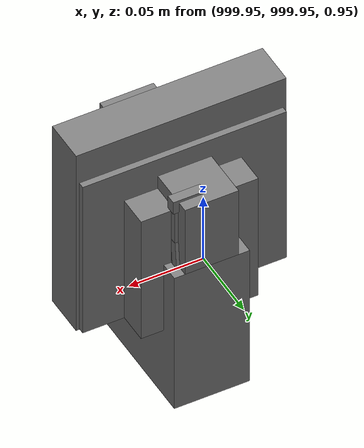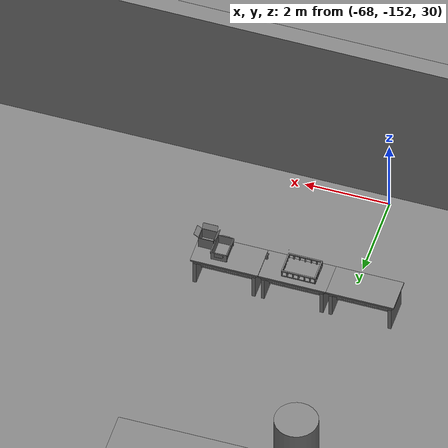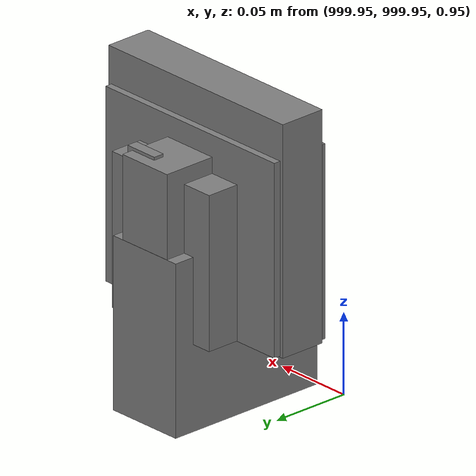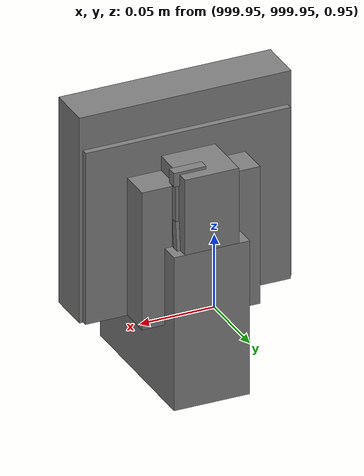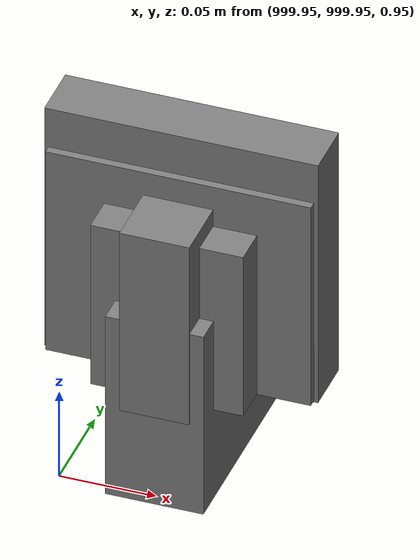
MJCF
<mujoco>
    <option gravity="0.000000000 0.000000000 -9.810000420" timestep="0.0049999999" integrator="implicitfast" density="1.225" viscosity="1.8000001e-05" noslip_iterations="10" iterations="100" sdf_iterations="50">
        <flag multiccd="disable"/>
    </option>
    <size memory="1000M"/>
    <compiler coordinate="local"/>
    <worldbody>
        <light cutoff="30" pos="0 1 1" dir="0 -1 -2"/>
        <light cutoff="30" pos="0 -1 1" dir="0 1 -2"/>
        <body pos="1000.000000000 1000.000000000 1.000000000" euler="0.000000000 0.000000000 180.000000000" name="openloong_gripper_2f85_fix_base_usda_cpu_fan">
            <geom contype="1" conaffinity="1" density="1000" type="box" material="" rgba="0.500000000 0.500000000 0.500000000 1.000000000" solimp="0.899999976 0.949999988 0.001000000" friction="1.000000000 0.005000000 0.000100000" solref="0.020000000 1.000000000" margin="0" condim="3" group="0" pos="0.000000000 0.000000000 0.070034981" quat="0.000000000 0.000000000 0.000000000 1.000000000" size="0.070700005 0.014699999 0.070700005" name="openloong_gripper_2f85_fix_base_usda_geom_A6B6725F_DC9E_4A81_B966_AFBD21399567"/>
            <freejoint name="openloong_gripper_2f85_fix_base_usda_cpu_fan_joint"/>
            <site size="0.005000000 0.005000000 0.005000000" rgba="0.500000000 0.500000000 0.500000000 1.000000000" pos="0.000000000 0.000000000 0.000000000" quat="0.999961913 0.008726535 0.000000000 0.000000000" group="0" type="sphere" name="openloong_gripper_2f85_fix_base_usda_cpu_fancsite"/>
        </body>
        <body pos="1000.000000000 1000.000000000 1.000000000" euler="0.000000000 0.000000000 180.000000000" name="openloong_gripper_2f85_fix_base_usda_wifi_box">
            <geom contype="1" conaffinity="1" density="1000" type="box" material="" rgba="0.500000000 0.500000000 0.500000000 1.000000000" solimp="0.899999976 0.949999988 0.001000000" friction="1.000000000 0.005000000 0.000100000" solref="0.020000000 1.000000000" margin="0" condim="3" group="0" pos="0.000000000 0.000000000 0.058978677" quat="0.000000000 0.000000047 0.000000000 1.000000000" size="0.068499997 0.018999999 0.059000000" name="openloong_gripper_2f85_fix_base_usda_geom_B4E402A0_352E_4340_AB68_E5F4E4837787"/>
            <freejoint name="openloong_gripper_2f85_fix_base_usda_wifi_box_joint"/>
            <site size="0.005000000 0.005000000 0.005000000" rgba="0.500000000 0.500000000 0.500000000 1.000000000" pos="0.000000000 0.000000000 0.000000000" quat="0.999961913 0.008726500 0.000000000 0.000000000" group="0" type="sphere" name="openloong_gripper_2f85_fix_base_usda_wifi_boxsite"/>
        </body>
        <body pos="1000.000000000 1000.000000000 1.000000000" euler="0.000011953 0.000005123 -179.999984741" name="openloong_gripper_2f85_fix_base_usda_intel_box">
            <geom contype="1" conaffinity="1" density="1000" type="box" material="" rgba="0.500000000 0.500000000 0.500000000 1.000000000" solimp="0.899999976 0.949999988 0.001000000" friction="1.000000000 0.005000000 0.000100000" solref="0.020000000 1.000000000" margin="0" condim="3" group="0" pos="0.000000000 -0.000067139 0.000082284" quat="0.707106709 0.000000225 0.000000253 0.707106650" size="0.052800003 0.025300000 0.052800003" name="openloong_gripper_2f85_fix_base_usda_geom_FE44BE27_AC9B_4BE8_90FD_E4EBBDA48494"/>
            <freejoint name="openloong_gripper_2f85_fix_base_usda_intel_box_joint"/>
            <site size="0.005000000 0.005000000 0.005000000" rgba="0.500000000 0.500000000 0.500000000 1.000000000" pos="0.000000000 0.000000000 0.000000000" quat="0.999961913 0.008726500 0.000000000 0.000000000" group="0" type="sphere" name="openloong_gripper_2f85_fix_base_usda_intel_boxsite"/>
        </body>
        <body pos="-66.203392029 -149.737136841 31.162094116" euler="-32.298603058 9.896430016 -178.260070801" mocap="true" name="spotlight5_SpotLight"/>
        <body pos="1000.000000000 999.999938965 1.000000000" euler="0.000000000 0.000000000 180.000000000" name="openloong_gripper_2f85_fix_base_usda_intelcore_i5">
            <geom contype="1" conaffinity="1" density="1000" type="box" material="" rgba="0.500000000 0.500000000 0.500000000 1.000000000" solimp="0.899999976 0.949999988 0.001000000" friction="1.000000000 0.005000000 0.000100000" solref="0.020000000 1.000000000" margin="0" condim="3" group="0" pos="0.000000000 0.000000000 0.051722717" quat="0.707106709 0.000000000 0.000000000 -0.707106769" size="0.052800000 0.018080002 0.052800000" name="openloong_gripper_2f85_fix_base_usda_geom_B9ED6AC0_AD63_474B_86B6_346DED5B4C4B"/>
            <freejoint name="openloong_gripper_2f85_fix_base_usda_intelcore_i5_joint"/>
            <site size="0.005000000 0.005000000 0.005000000" rgba="0.500000000 0.500000000 0.500000000 1.000000000" pos="0.000000000 0.000000000 0.000000000" quat="0.999961913 0.008726534 0.000000000 0.000000000" group="0" type="sphere" name="openloong_gripper_2f85_fix_base_usda_intelcore_i5site"/>
        </body>
        <body pos="-66.157844543 -149.457077026 31.168865204" euler="48.950366974 74.143135071 -176.189208984" mocap="true" name="spotlight2_SpotLight"/>
        <body pos="1000.000000000 1000.000000000 1.000000000" euler="0.000000000 0.000000000 180.000000000" name="openloong_gripper_2f85_fix_base_usda_battery_01">
            <geom contype="1" conaffinity="1" density="1000" type="box" material="" rgba="0.500000000 0.500000000 0.500000000 1.000000000" solimp="0.899999976 0.949999988 0.001000000" friction="1.000000000 0.005000000 0.000100000" solref="0.020000000 1.000000000" margin="0" condim="3" group="0" pos="-0.011123657 -0.041940309 0.101691343" quat="1.000000000 0.000000000 0.000000000 0.000000000" size="0.010800000 0.003375000 0.004725000" name="openloong_gripper_2f85_fix_base_usda_geom_03496DB8_D83F_413F_8C06_0AE1F9FD70E3"/>
            <geom contype="1" conaffinity="1" density="1000" type="box" material="" rgba="0.500000000 0.500000000 0.500000000 1.000000000" solimp="0.899999976 0.949999988 0.001000000" friction="1.000000000 0.005000000 0.000100000" solref="0.020000000 1.000000000" margin="0" condim="3" group="0" pos="-0.010876465 -0.044247437 0.047066893" quat="0.998702705 -0.050920475 0.000000000 0.000000000" size="0.009450001 0.002700000 0.024975000" name="openloong_gripper_2f85_fix_base_usda_geom_A1718801_D599_4524_A4BA_1FB13DEF8699"/>
            <geom contype="1" conaffinity="1" density="1000" type="box" material="" rgba="0.500000000 0.500000000 0.500000000 1.000000000" solimp="0.899999976 0.949999988 0.001000000" friction="1.000000000 0.005000000 0.000100000" solref="0.020000000 1.000000000" margin="0" condim="3" group="0" pos="-0.001235962 -0.000659180 0.047381196" quat="1.000000000 0.000000000 0.000000000 0.000000000" size="0.039420001 0.039150000 0.047250003" name="openloong_gripper_2f85_fix_base_usda_geom_6FB65438_F118_434D_BAB0_98BDC86620E2"/>
            <geom contype="1" conaffinity="1" density="1000" type="box" material="" rgba="0.500000000 0.500000000 0.500000000 1.000000000" solimp="0.899999976 0.949999988 0.001000000" friction="1.000000000 0.005000000 0.000100000" solref="0.020000000 1.000000000" margin="0" condim="3" group="0" pos="-0.010876465 -0.039138794 0.009851727" quat="1.000000000 0.000000000 0.000000000 0.000000000" size="0.009450001 0.010800000 0.013500000" name="openloong_gripper_2f85_fix_base_usda_geom_AEE9B0A2_C737_4A4F_8787_01A630298C37"/>
            <geom contype="1" conaffinity="1" density="1000" type="box" material="" rgba="0.500000000 0.500000000 0.500000000 1.000000000" solimp="0.899999976 0.949999988 0.001000000" friction="1.000000000 0.005000000 0.000100000" solref="0.020000000 1.000000000" margin="0" condim="3" group="0" pos="-0.010876465 -0.041528322 0.071508206" quat="1.000000000 0.000000000 0.000000000 0.000000000" size="0.009450001 0.002700000 0.027000001" name="openloong_gripper_2f85_fix_base_usda_geom_30C40799_B4BA_44A1_9A5C_B7976F9CFE7F"/>
            <freejoint name="openloong_gripper_2f85_fix_base_usda_battery_01_joint"/>
            <site size="0.005000000 0.005000000 0.005000000" rgba="0.500000000 0.500000000 0.500000000 1.000000000" pos="0.000000000 0.000000000 0.000000000" quat="0.999961913 0.008726500 0.000000000 0.000000000" group="0" type="sphere" name="openloong_gripper_2f85_fix_base_usda_battery_01site"/>
        </body>
        <body pos="-66.097946167 -149.017745972 31.166143417" euler="40.430732727 64.087295532 173.015243530" mocap="true" name="spotlight4_SpotLight"/>
        <body pos="-64.866622925 -149.383972168 30.183746338" euler="89.999984741 89.999946594 0.000000000" name="openloong_gripper_2f85_fix_base_usda_bluebox_01">
            <geom contype="1" conaffinity="1" density="1000" type="box" material="" rgba="0.500000000 0.500000000 0.500000000 1.000000000" solimp="0.899999976 0.949999988 0.001000000" friction="1.000000000 0.005000000 0.000100000" solref="0.020000000 1.000000000" margin="0" condim="3" group="0" pos="0.276580811 0.187225342 0.000068665" quat="0.707106948 0.000077471 0.707106352 0.000077486" size="0.100000001 0.057999998 0.010000000" name="openloong_gripper_2f85_fix_base_usda_geom_D2EAA8F3_3852_4C8C_980F_F8C27E1ACBA7"/>
            <geom contype="1" conaffinity="1" density="1000" type="box" material="" rgba="0.500000000 0.500000000 0.500000000 1.000000000" solimp="0.899999976 0.949999988 0.001000000" friction="1.000000000 0.005000000 0.000100000" solref="0.020000000 1.000000000" margin="0" condim="3" group="0" pos="0.000000000 0.002883911 0.000000000" quat="0.999999881 0.000000000 0.000000000 0.000000000" size="0.254000008 0.003000000 0.172000006" name="openloong_gripper_2f85_fix_base_usda_geom_7C35D400_3183_4E3D_8F9D_EAAE5725F4E1"/>
            <geom contype="1" conaffinity="1" density="1000" type="box" material="" rgba="0.500000000 0.500000000 0.500000000 1.000000000" solimp="0.899999976 0.949999988 0.001000000" friction="1.000000000 0.005000000 0.000100000" solref="0.020000000 1.000000000" margin="0" condim="3" group="0" pos="0.000000000 0.124874115 0.173484802" quat="0.999796331 0.020176515 -0.000000015 0.000000030" size="0.259999990 0.119999997 0.007000000" name="openloong_gripper_2f85_fix_base_usda_geom_8C3EAEE0_C0D5_4FF4_9218_F910087EA120"/>
            <geom contype="1" conaffinity="1" density="1000" type="box" material="" rgba="0.500000000 0.500000000 0.500000000 1.000000000" solimp="0.899999976 0.949999988 0.001000000" friction="1.000000000 0.005000000 0.000100000" solref="0.020000000 1.000000000" margin="0" condim="3" group="0" pos="0.000000000 0.124874115 -0.173469543" quat="0.999796331 -0.020176545 -0.000000015 0.000000000" size="0.259999990 0.119999997 0.007000000" name="openloong_gripper_2f85_fix_base_usda_geom_3D816786_21E4_4839_A2F9_C4C33183A4EC"/>
            <geom contype="1" conaffinity="1" density="1000" type="box" material="" rgba="0.500000000 0.500000000 0.500000000 1.000000000" solimp="0.899999976 0.949999988 0.001000000" friction="1.000000000 0.005000000 0.000100000" solref="0.020000000 1.000000000" margin="0" condim="3" group="0" pos="0.000000000 0.214008331 0.188980103" quat="0.999912977 0.013176724 0.000000015 0.000000000" size="0.259999990 0.029999999 0.012500000" name="openloong_gripper_2f85_fix_base_usda_geom_3EDA67C7_0122_4CA6_8148_4B8C8D4D1F64"/>
            <geom contype="1" conaffinity="1" density="1000" type="box" material="" rgba="0.500000000 0.500000000 0.500000000 1.000000000" solimp="0.899999976 0.949999988 0.001000000" friction="1.000000000 0.005000000 0.000100000" solref="0.020000000 1.000000000" margin="0" condim="3" group="0" pos="-0.258361816 0.125289917 0.001876831" quat="0.702796936 -0.020792112 0.710783124 0.020769298" size="0.189999998 0.119999997 0.009000000" name="openloong_gripper_2f85_fix_base_usda_geom_DB34ECF2_055D_48DC_A01D_0B84F936B019"/>
            <geom contype="1" conaffinity="1" density="1000" type="box" material="" rgba="0.500000000 0.500000000 0.500000000 1.000000000" solimp="0.899999976 0.949999988 0.001000000" friction="1.000000000 0.005000000 0.000100000" solref="0.020000000 1.000000000" margin="0" condim="3" group="0" pos="0.000000000 0.214008331 -0.188980103" quat="0.999912977 -0.013176769 0.000000030 0.000000015" size="0.259999990 0.029999999 0.012500000" name="openloong_gripper_2f85_fix_base_usda_geom_27525CEE_0560_4D63_897B_9A87A94BE101"/>
            <geom contype="1" conaffinity="1" density="1000" type="box" material="" rgba="0.500000000 0.500000000 0.500000000 1.000000000" solimp="0.899999976 0.949999988 0.001000000" friction="1.000000000 0.005000000 0.000100000" solref="0.020000000 1.000000000" margin="0" condim="3" group="0" pos="-0.276611328 0.187225342 0.000068665" quat="0.707106650 0.000077441 0.707106709 0.000077456" size="0.100000001 0.057999998 0.010000000" name="openloong_gripper_2f85_fix_base_usda_geom_AAB1884B_0364_4768_9511_9F7E9B0AD79E"/>
            <geom contype="1" conaffinity="1" density="1000" type="box" material="" rgba="0.500000000 0.500000000 0.500000000 1.000000000" solimp="0.899999976 0.949999988 0.001000000" friction="1.000000000 0.005000000 0.000100000" solref="0.020000000 1.000000000" margin="0" condim="3" group="0" pos="0.258331299 0.125289917 0.001876831" quat="0.702851415 0.018856421 0.710823774 -0.019329369" size="0.189999998 0.119999997 0.009000000" name="openloong_gripper_2f85_fix_base_usda_geom_C4ABC14D_409B_4E38_BD9E_25DA32F25D10"/>
            <freejoint name="openloong_gripper_2f85_fix_base_usda_bluebox_01_joint"/>
            <site size="0.005000000 0.005000000 0.005000000" rgba="0.500000000 0.500000000 0.500000000 1.000000000" pos="0.000000000 0.000000000 0.000000000" quat="0.999961913 0.008726534 0.000000000 0.000000000" group="0" type="sphere" name="openloong_gripper_2f85_fix_base_usda_bluebox_01site"/>
        </body>
        <body pos="-64.496299744 -149.491867065 30.235729218" euler="0.000000000 0.000000000 89.999946594" name="openloong_gripper_2f85_fix_base_usda_cardboardbox_01">
            <geom contype="1" conaffinity="1" density="1000" type="box" material="" rgba="0.500000000 0.500000000 0.500000000 1.000000000" solimp="0.899999976 0.949999988 0.001000000" friction="1.000000000 0.005000000 0.000100000" solref="0.020000000 1.000000000" margin="0" condim="3" group="0" pos="-0.003166199 -0.004086494 0.005052090" quat="1.000000000 0.000000000 0.000000000 0.000000000" size="0.142499998 0.177500010 0.005000000" name="openloong_gripper_2f85_fix_base_usda_geom_20B0BC22_DE44_4ABF_8506_EBB8AC78AEAA"/>
            <geom contype="1" conaffinity="1" density="1000" type="box" material="" rgba="0.500000000 0.500000000 0.500000000 1.000000000" solimp="0.899999976 0.949999988 0.001000000" friction="1.000000000 0.005000000 0.000100000" solref="0.020000000 1.000000000" margin="0" condim="3" group="0" pos="-0.003166199 0.170316696 0.150570869" quat="1.000000000 0.000000000 0.000000000 0.000000000" size="0.142499998 0.005000000 0.149999991" name="openloong_gripper_2f85_fix_base_usda_geom_E5321910_344D_4945_9630_225E964A0572"/>
            <geom contype="1" conaffinity="1" density="1000" type="box" material="" rgba="0.500000000 0.500000000 0.500000000 1.000000000" solimp="0.899999976 0.949999988 0.001000000" friction="1.000000000 0.005000000 0.000100000" solref="0.020000000 1.000000000" margin="0" condim="3" group="0" pos="-0.147399902 -0.005307198 0.150570869" quat="1.000000000 0.000000000 0.000000000 0.000000000" size="0.005000000 0.177500010 0.149999991" name="openloong_gripper_2f85_fix_base_usda_geom_A8E89D20_8C22_4DAE_85E4_3EBEB1AED34C"/>
            <geom contype="1" conaffinity="1" density="1000" type="box" material="" rgba="0.500000000 0.500000000 0.500000000 1.000000000" solimp="0.899999976 0.949999988 0.001000000" friction="1.000000000 0.005000000 0.000100000" solref="0.020000000 1.000000000" margin="0" condim="3" group="0" pos="0.140275955 -0.005307198 0.150570869" quat="1.000000000 0.000000000 0.000000000 0.000000000" size="0.005000000 0.177500010 0.149999991" name="openloong_gripper_2f85_fix_base_usda_geom_7BB0B390_AFDD_4120_A163_41BBF08E6689"/>
            <geom contype="1" conaffinity="1" density="1000" type="box" material="" rgba="0.500000000 0.500000000 0.500000000 1.000000000" solimp="0.899999976 0.949999988 0.001000000" friction="1.000000000 0.005000000 0.000100000" solref="0.020000000 1.000000000" margin="0" condim="3" group="0" pos="-0.003166199 -0.181550980 0.150570869" quat="1.000000000 0.000000000 0.000000000 0.000000000" size="0.142499998 0.005000000 0.149999991" name="openloong_gripper_2f85_fix_base_usda_geom_662B76CA_67CA_4DA2_95F7_6847AB983E76"/>
            <freejoint name="openloong_gripper_2f85_fix_base_usda_cardboardbox_01_joint"/>
            <site size="0.005000000 0.005000000 0.005000000" rgba="0.500000000 0.500000000 0.500000000 1.000000000" pos="0.000000000 0.000000000 0.000000000" quat="0.999961913 0.008726535 0.000000000 0.000000000" group="0" type="sphere" name="openloong_gripper_2f85_fix_base_usda_site_14123D50_1B54_4BB2_B0E3_95F196F9861F"/>
            <body pos="0.139160156 -0.004048347 0.301930904" euler="-179.999954224 49.383502960 179.999954224" name="openloong_gripper_2f85_fix_base_usda_A1_006">
                <geom contype="1" conaffinity="1" density="1000" type="box" material="" rgba="0.500000000 0.500000000 0.500000000 1.000000000" solimp="0.899999976 0.949999988 0.001000000" friction="1.000000000 0.005000000 0.000100000" solref="0.020000000 1.000000000" margin="0" condim="3" group="0" pos="-0.071587563 0.000009537 0.001745224" quat="0.999999881 0.000000000 0.000000000 0.000000000" size="0.071249999 0.179999992 0.002500000" name="openloong_gripper_2f85_fix_base_usda_geom_5843CFC0_A677_401C_8CDB_47D6EB77BB01"/>
                <joint armature="0" stiffness="0.07" damping="0.0099999998" axis="0.000000 1.000000 0.000000" type="hinge" name="openloong_gripper_2f85_fix_base_usda_A1_006"/>
            </body>
            <body pos="-0.145902634 -0.004086494 0.301938057" euler="-180.000000000 -60.000011444 -180.000000000" name="openloong_gripper_2f85_fix_base_usda_A2_006">
                <geom contype="1" conaffinity="1" density="1000" type="box" material="" rgba="0.500000000 0.500000000 0.500000000 1.000000000" solimp="0.899999976 0.949999988 0.001000000" friction="1.000000000 0.005000000 0.000100000" solref="0.020000000 1.000000000" margin="0" condim="3" group="0" pos="0.071268082 0.000009537 0.002717972" quat="0.000002921 0.000000000 -0.000000030 0.999999881" size="0.071249999 0.179999992 0.002500000" name="openloong_gripper_2f85_fix_base_usda_geom_87BAC0CB_6313_4094_AAAB_AE96F09E6540"/>
                <joint armature="0" stiffness="0.07" damping="0.0099999998" axis="0.000000 1.000000 0.000000" type="hinge" name="openloong_gripper_2f85_fix_base_usda_A2_006"/>
            </body>
            <body pos="-0.003385544 0.175991058 0.301930904" euler="-125.858116150 -0.000004561 0.000002331" name="openloong_gripper_2f85_fix_base_usda_B2_006">
                <geom contype="1" conaffinity="1" density="1000" type="box" material="" rgba="0.500000000 0.500000000 0.500000000 1.000000000" solimp="0.899999976 0.949999988 0.001000000" friction="1.000000000 0.005000000 0.000100000" solref="0.020000000 1.000000000" margin="0" condim="3" group="0" pos="0.000009537 -0.070939064 -0.002470016" quat="0.999614120 0.027776197 -0.000000015 0.000000030" size="0.137500003 0.064999998 0.005000000" name="openloong_gripper_2f85_fix_base_usda_geom_43F78630_1D31_4A0F_A413_E15C2FE128EB"/>
                <joint armature="0" stiffness="0.07" damping="0.0099999998" axis="1.000000 0.000000 0.000000" type="hinge" name="openloong_gripper_2f85_fix_base_usda_B2_006"/>
            </body>
            <body pos="-0.003385544 -0.184140205 0.301938057" euler="147.805557251 0.000000000 0.000000000" name="openloong_gripper_2f85_fix_base_usda_B1_006">
                <geom contype="1" conaffinity="1" density="1000" type="box" material="" rgba="0.500000000 0.500000000 0.500000000 1.000000000" solimp="0.899999976 0.949999988 0.001000000" friction="1.000000000 0.005000000 0.000100000" solref="0.020000000 1.000000000" margin="0" condim="3" group="0" pos="-0.000028610 0.070202351 -0.002703667" quat="0.999614179 -0.027776167 0.000000000 0.000000000" size="0.137500003 0.064999998 0.005000000" name="openloong_gripper_2f85_fix_base_usda_geom_E30C47D6_88BB_4507_AC95_7F4AF9DF3D79"/>
                <joint armature="0" stiffness="0.07" damping="0.0099999998" axis="1.000000 0.000000 0.000000" type="hinge" name="openloong_gripper_2f85_fix_base_usda_B1_006"/>
            </body>
        </body>
        <body pos="-65.882858276 -149.481979370 30.229999542" euler="-64.487716675 0.000000000 0.000000000" name="openloong_gripper_2f85_fix_base_usda_Barcode">
            <geom contype="1" conaffinity="1" density="1000" type="box" material="" rgba="0.500000000 0.500000000 0.500000000 1.000000000" solimp="0.899999976 0.949999988 0.001000000" friction="1.000000000 0.005000000 0.000100000" solref="0.020000000 1.000000000" margin="0" condim="3" group="0" pos="0.000000000 0.013038635 0.001419067" quat="0.000000000 0.000000000 0.000000000 1.000000119" size="0.034000002 0.010000000 0.017999999" name="openloong_gripper_2f85_fix_base_usda_geom_089E8526_7FE3_4517_A51C_514E3A95D58B"/>
            <geom contype="1" conaffinity="1" density="1000" type="box" material="" rgba="0.500000000 0.500000000 0.500000000 1.000000000" solimp="0.899999976 0.949999988 0.001000000" friction="1.000000000 0.005000000 0.000100000" solref="0.020000000 1.000000000" margin="0" condim="3" group="0" pos="0.000000000 -0.035301208 -0.007095337" quat="0.000000000 0.000000000 -0.043619365 0.999048233" size="0.028999999 0.010000000 0.020000000" name="openloong_gripper_2f85_fix_base_usda_geom_D94B83FC_0CA2_4162_A22A_DB516D214C08"/>
            <geom contype="1" conaffinity="1" density="1000" type="box" material="" rgba="0.500000000 0.500000000 0.500000000 1.000000000" solimp="0.899999976 0.949999988 0.001000000" friction="1.000000000 0.005000000 0.000100000" solref="0.020000000 1.000000000" margin="0" condim="3" group="0" pos="0.000000000 -0.043411255 -0.011749268" quat="0.922262907 0.386563420 0.000000000 0.000000000" size="0.026000001 0.010000000 0.020000000" name="openloong_gripper_2f85_fix_base_usda_geom_D7786C64_8977_431A_98C9_EC9FEC14408F"/>
            <geom contype="1" conaffinity="1" density="1000" type="box" material="" rgba="0.500000000 0.500000000 0.500000000 1.000000000" solimp="0.899999976 0.949999988 0.001000000" friction="1.000000000 0.005000000 0.000100000" solref="0.020000000 1.000000000" margin="0" condim="3" group="0" pos="0.000000000 -0.016967773 -0.031860352" quat="0.000000000 0.000000000 0.000000000 1.000000119" size="0.008000000 0.010000000 0.013000000" name="openloong_gripper_2f85_fix_base_usda_geom_55DD6C1F_A17C_4F2D_8199_058799883F25"/>
            <geom contype="1" conaffinity="1" density="1000" type="box" material="" rgba="0.500000000 0.500000000 0.500000000 1.000000000" solimp="0.899999976 0.949999988 0.001000000" friction="1.000000000 0.005000000 0.000100000" solref="0.020000000 1.000000000" margin="0" condim="3" group="0" pos="0.000000000 -0.001869202 0.000312805" quat="0.953716993 0.300705761 0.000000000 0.000000000" size="0.032000002 0.010000000 0.018999999" name="openloong_gripper_2f85_fix_base_usda_geom_5125A27F_2E73_4995_96FF_B9AA7951642A"/>
            <geom contype="1" conaffinity="1" density="1000" type="box" material="" rgba="0.500000000 0.500000000 0.500000000 1.000000000" solimp="0.899999976 0.949999988 0.001000000" friction="1.000000000 0.005000000 0.000100000" solref="0.020000000 1.000000000" margin="0" condim="3" group="0" pos="0.000000000 -0.019531250 -0.003173828" quat="0.953716993 0.300705761 0.000000000 0.000000000" size="0.030999999 0.010000000 0.020000000" name="openloong_gripper_2f85_fix_base_usda_geom_637E8B7C_BD20_4A16_BA5D_6817A1030A50"/>
            <geom contype="1" conaffinity="1" density="1000" type="box" material="" rgba="0.500000000 0.500000000 0.500000000 1.000000000" solimp="0.899999976 0.949999988 0.001000000" friction="1.000000000 0.005000000 0.000100000" solref="0.020000000 1.000000000" margin="0" condim="3" group="0" pos="0.000000000 -0.035301208 -0.007095337" quat="0.953716993 0.300705761 0.000000000 0.000000000" size="0.028999999 0.010000000 0.020000000" name="openloong_gripper_2f85_fix_base_usda_geom_D3427EC9_63DF_4F60_BF63_7E00766577A7"/>
            <geom contype="1" conaffinity="1" density="1000" type="box" material="" rgba="0.500000000 0.500000000 0.500000000 1.000000000" solimp="0.899999976 0.949999988 0.001000000" friction="1.000000000 0.005000000 0.000100000" solref="0.020000000 1.000000000" margin="0" condim="3" group="0" pos="0.000000000 -0.042617798 -0.071121216" quat="0.000000000 0.000000000 0.000000000 1.000000119" size="0.013000000 0.021000000 0.059999999" name="openloong_gripper_2f85_fix_base_usda_geom_6FCEF77D_35B2_4856_AEF6_7DB97D22C12B"/>
            <freejoint name="openloong_gripper_2f85_fix_base_usda_Barcode_joint"/>
            <site size="0.005000000 0.005000000 0.005000000" rgba="0.500000000 0.500000000 0.500000000 1.000000000" pos="0.000000000 0.000000000 0.000000000" quat="1.000000000 0.000000000 0.000000000 0.000000000" group="0" type="sphere" name="openloong_gripper_2f85_fix_base_usda_Barcode_site"/>
        </body>
        <body pos="-66.745018005 -149.392349243 30.184000015" euler="0.000000000 0.000000000 89.999946594" name="[22333332698873]_Basket_01">
            <geom contype="1" conaffinity="1" density="1000" type="box" material="" rgba="0.500000000 0.500000000 0.500000000 1.000000000" solimp="0.899999976 0.949999988 0.001000000" friction="1.000000000 0.005000000 0.000100000" solref="0.020000000 1.000000000" margin="0" condim="3" group="0" pos="-0.052425385 0.389207840 0.089787483" quat="0.707107008 0.000000000 0.000000000 0.707106411" size="0.014249999 0.014249999 0.059999999" name="[22333332698873]_geom_C7B3DAE4_FF11_4B51_9496_29074F8B13F0"/>
            <geom contype="1" conaffinity="1" density="1000" type="box" material="" rgba="0.500000000 0.500000000 0.500000000 1.000000000" solimp="0.899999976 0.949999988 0.001000000" friction="1.000000000 0.005000000 0.000100000" solref="0.020000000 1.000000000" margin="0" condim="3" group="0" pos="0.264015198 -0.133043289 0.089787483" quat="0.707107008 0.000000000 0.000000000 0.707106411" size="0.014249999 0.014249999 0.059999999" name="[22333332698873]_geom_365E7A41_DEF5_4BEC_AEA8_E5364D72863B"/>
            <geom contype="1" conaffinity="1" density="1000" type="box" material="" rgba="0.500000000 0.500000000 0.500000000 1.000000000" solimp="0.899999976 0.949999988 0.001000000" friction="1.000000000 0.005000000 0.000100000" solref="0.020000000 1.000000000" margin="0" condim="3" group="0" pos="-0.264015198 -0.265548706 0.089793205" quat="0.707107008 0.000000000 0.000000000 0.707106411" size="0.014249999 0.014249999 0.059999999" name="[22333332698873]_geom_A487F150_5422_4D1A_A8C5_304015807775"/>
            <geom contype="1" conaffinity="1" density="1000" type="box" material="" rgba="0.500000000 0.500000000 0.500000000 1.000000000" solimp="0.899999976 0.949999988 0.001000000" friction="1.000000000 0.005000000 0.000100000" solref="0.020000000 1.000000000" margin="0" condim="3" group="0" pos="-0.160263062 -0.389322281 0.089793205" quat="0.707107008 0.000000000 0.000000000 0.707106411" size="0.014249999 0.014249999 0.059999999" name="[22333332698873]_geom_0ED3729A_432E_4963_8FC2_205CD04FBB5F"/>
            <geom contype="1" conaffinity="1" density="1000" type="box" material="" rgba="0.500000000 0.500000000 0.500000000 1.000000000" solimp="0.899999976 0.949999988 0.001000000" friction="1.000000000 0.005000000 0.000100000" solref="0.020000000 1.000000000" margin="0" condim="3" group="0" pos="0.162265778 -0.389322281 0.089787483" quat="0.707107008 0.000000000 0.000000000 0.707106411" size="0.014249999 0.014249999 0.059999999" name="[22333332698873]_geom_DB76FEE3_A46E_429C_89D2_4ADA8DE6C58B"/>
            <geom contype="1" conaffinity="1" density="1000" type="box" material="" rgba="0.500000000 0.500000000 0.500000000 1.000000000" solimp="0.899999976 0.949999988 0.001000000" friction="1.000000000 0.005000000 0.000100000" solref="0.020000000 1.000000000" margin="0" condim="3" group="0" pos="0.264015198 0.389207840 0.089787483" quat="0.707107008 0.000000000 0.000000000 0.707106411" size="0.014249999 0.014249999 0.059999999" name="[22333332698873]_geom_710745FA_25C1_4E11_B175_E1AF24A26690"/>
            <geom contype="1" conaffinity="1" density="1000" type="box" material="" rgba="0.500000000 0.500000000 0.500000000 1.000000000" solimp="0.899999976 0.949999988 0.001000000" friction="1.000000000 0.005000000 0.000100000" solref="0.020000000 1.000000000" margin="0" condim="3" group="0" pos="-0.264015198 -0.133043289 0.089793205" quat="0.707107008 0.000000000 0.000000000 0.707106411" size="0.014249999 0.014249999 0.059999999" name="[22333332698873]_geom_DCC939C7_51A7_4E13_9751_082CF9457FE4"/>
            <geom contype="1" conaffinity="1" density="1000" type="box" material="" rgba="0.500000000 0.500000000 0.500000000 1.000000000" solimp="0.899999976 0.949999988 0.001000000" friction="1.000000000 0.005000000 0.000100000" solref="0.020000000 1.000000000" margin="0" condim="3" group="0" pos="-0.264026642 0.269256592 0.089793205" quat="0.707107008 0.000000000 0.000000000 0.707106411" size="0.014249999 0.014249999 0.059999999" name="[22333332698873]_geom_4D1ABC39_AEC9_43E6_9FDA_A87D318793D8"/>
            <geom contype="1" conaffinity="1" density="1000" type="box" material="" rgba="0.500000000 0.500000000 0.500000000 1.000000000" solimp="0.899999976 0.949999988 0.001000000" friction="1.000000000 0.005000000 0.000100000" solref="0.020000000 1.000000000" margin="0" condim="3" group="0" pos="0.054462433 0.389207840 0.089787483" quat="0.707107008 0.000000000 0.000000000 0.707106411" size="0.014249999 0.014249999 0.059999999" name="[22333332698873]_geom_B89A2319_B9D0_4852_AAB6_9DD574FBD8C6"/>
            <geom contype="1" conaffinity="1" density="1000" type="box" material="" rgba="0.500000000 0.500000000 0.500000000 1.000000000" solimp="0.899999976 0.949999988 0.001000000" friction="1.000000000 0.005000000 0.000100000" solref="0.020000000 1.000000000" margin="0" condim="3" group="0" pos="0.054462433 -0.389322281 0.089787483" quat="0.707107008 0.000000000 0.000000000 0.707106411" size="0.014249999 0.014249999 0.059999999" name="[22333332698873]_geom_FB27CDCC_A31C_45C4_8B73_D038F1D36124"/>
            <geom contype="1" conaffinity="1" density="1000" type="box" material="" rgba="0.500000000 0.500000000 0.500000000 1.000000000" solimp="0.899999976 0.949999988 0.001000000" friction="1.000000000 0.005000000 0.000100000" solref="0.020000000 1.000000000" margin="0" condim="3" group="0" pos="0.264015198 0.269256592 0.089793205" quat="0.707107008 0.000000000 0.000000000 0.707106411" size="0.014249999 0.014249999 0.059999999" name="[22333332698873]_geom_FC250409_D2A4_451C_AFC0_2BA96442C686"/>
            <geom contype="1" conaffinity="1" density="1000" type="box" material="" rgba="0.500000000 0.500000000 0.500000000 1.000000000" solimp="0.899999976 0.949999988 0.001000000" friction="1.000000000 0.005000000 0.000100000" solref="0.020000000 1.000000000" margin="0" condim="3" group="0" pos="0.264015198 -0.389322281 0.089787483" quat="0.707107008 0.000000000 0.000000000 0.707106411" size="0.014249999 0.014249999 0.059999999" name="[22333332698873]_geom_17FCD6C4_0D94_44B9_ABD3_59C09CF89E7C"/>
            <geom contype="1" conaffinity="1" density="1000" type="box" material="" rgba="0.500000000 0.500000000 0.500000000 1.000000000" solimp="0.899999976 0.949999988 0.001000000" friction="1.000000000 0.005000000 0.000100000" solref="0.020000000 1.000000000" margin="0" condim="3" group="0" pos="0.000000000 0.000000000 0.015998840" quat="0.707107008 0.000000000 0.000000000 0.707106411" size="0.403499991 0.279000014 0.015750000" name="[22333332698873]_geom_858DCA7C_43A2_4D90_BE4F_782516BBDC37"/>
            <geom contype="1" conaffinity="1" density="1000" type="box" material="" rgba="0.500000000 0.500000000 0.500000000 1.000000000" solimp="0.899999976 0.949999988 0.001000000" friction="1.000000000 0.005000000 0.000100000" solref="0.020000000 1.000000000" margin="0" condim="3" group="0" pos="0.000000000 -0.389476776 0.163619041" quat="0.707107008 0.000000000 0.000000000 0.707106411" size="0.015000000 0.277500004 0.015750000" name="[22333332698873]_geom_B5B2549A_0C84_4B85_86B9_27361F549EA0"/>
            <geom contype="1" conaffinity="1" density="1000" type="box" material="" rgba="0.500000000 0.500000000 0.500000000 1.000000000" solimp="0.899999976 0.949999988 0.001000000" friction="1.000000000 0.005000000 0.000100000" solref="0.020000000 1.000000000" margin="0" condim="3" group="0" pos="0.162265778 0.389207840 0.089787483" quat="0.707107008 0.000000000 0.000000000 0.707106411" size="0.014249999 0.014249999 0.059999999" name="[22333332698873]_geom_A7DEE720_449E_4963_80AB_4A8D8B4921DE"/>
            <geom contype="1" conaffinity="1" density="1000" type="box" material="" rgba="0.500000000 0.500000000 0.500000000 1.000000000" solimp="0.899999976 0.949999988 0.001000000" friction="1.000000000 0.005000000 0.000100000" solref="0.020000000 1.000000000" margin="0" condim="3" group="0" pos="0.000000000 0.389471054 0.163619041" quat="0.707107008 0.000000000 0.000000000 0.707106411" size="0.015000000 0.277500004 0.015750000" name="[22333332698873]_geom_F3ACA9CE_377A_420C_BD1D_79CB73C946F6"/>
            <geom contype="1" conaffinity="1" density="1000" type="box" material="" rgba="0.500000000 0.500000000 0.500000000 1.000000000" solimp="0.899999976 0.949999988 0.001000000" friction="1.000000000 0.005000000 0.000100000" solref="0.020000000 1.000000000" margin="0" condim="3" group="0" pos="-0.263511658 0.000000000 0.163619041" quat="0.707107008 0.000000000 0.000000000 0.707106411" size="0.403499991 0.015000000 0.015750000" name="[22333332698873]_geom_89E58ADA_5533_4590_A463_265511BDA75B"/>
            <geom contype="1" conaffinity="1" density="1000" type="box" material="" rgba="0.500000000 0.500000000 0.500000000 1.000000000" solimp="0.899999976 0.949999988 0.001000000" friction="1.000000000 0.005000000 0.000100000" solref="0.020000000 1.000000000" margin="0" condim="3" group="0" pos="-0.264015198 0.141334534 0.089793205" quat="0.707107008 0.000000000 0.000000000 0.707106411" size="0.014249999 0.014249999 0.059999999" name="[22333332698873]_geom_AD510303_6FC2_4931_9F6C_FC17D70CC373"/>
            <geom contype="1" conaffinity="1" density="1000" type="box" material="" rgba="0.500000000 0.500000000 0.500000000 1.000000000" solimp="0.899999976 0.949999988 0.001000000" friction="1.000000000 0.005000000 0.000100000" solref="0.020000000 1.000000000" margin="0" condim="3" group="0" pos="0.264015198 -0.265548706 0.089787483" quat="0.707107008 0.000000000 0.000000000 0.707106411" size="0.014249999 0.014249999 0.059999999" name="[22333332698873]_geom_91367712_08E0_4B34_8568_FC9EE0D37AA1"/>
            <geom contype="1" conaffinity="1" density="1000" type="box" material="" rgba="0.500000000 0.500000000 0.500000000 1.000000000" solimp="0.899999976 0.949999988 0.001000000" friction="1.000000000 0.005000000 0.000100000" solref="0.020000000 1.000000000" margin="0" condim="3" group="0" pos="-0.160263062 0.389207840 0.089787483" quat="0.707107008 0.000000000 0.000000000 0.707106411" size="0.014249999 0.014249999 0.059999999" name="[22333332698873]_geom_2EF0281E_7F67_4B8F_8471_72C1C1678E89"/>
            <geom contype="1" conaffinity="1" density="1000" type="box" material="" rgba="0.500000000 0.500000000 0.500000000 1.000000000" solimp="0.899999976 0.949999988 0.001000000" friction="1.000000000 0.005000000 0.000100000" solref="0.020000000 1.000000000" margin="0" condim="3" group="0" pos="-0.052425385 -0.389322281 0.089787483" quat="0.707107008 0.000000000 0.000000000 0.707106411" size="0.014249999 0.014249999 0.059999999" name="[22333332698873]_geom_A8A354C8_69E8_4F55_ACED_56BA470C4CF1"/>
            <geom contype="1" conaffinity="1" density="1000" type="box" material="" rgba="0.500000000 0.500000000 0.500000000 1.000000000" solimp="0.899999976 0.949999988 0.001000000" friction="1.000000000 0.005000000 0.000100000" solref="0.020000000 1.000000000" margin="0" condim="3" group="0" pos="-0.264026642 -0.389322281 0.089793205" quat="0.707107008 0.000000000 0.000000000 0.707106411" size="0.014249999 0.014249999 0.059999999" name="[22333332698873]_geom_F8D199F4_90A9_4522_B587_E20B76EA12FB"/>
            <geom contype="1" conaffinity="1" density="1000" type="box" material="" rgba="0.500000000 0.500000000 0.500000000 1.000000000" solimp="0.899999976 0.949999988 0.001000000" friction="1.000000000 0.005000000 0.000100000" solref="0.020000000 1.000000000" margin="0" condim="3" group="0" pos="0.264015198 0.141334534 0.089787483" quat="0.707107008 0.000000000 0.000000000 0.707106411" size="0.014249999 0.014249999 0.059999999" name="[22333332698873]_geom_AD7E6573_0E86_44B4_B130_92186AB08FDA"/>
            <geom contype="1" conaffinity="1" density="1000" type="box" material="" rgba="0.500000000 0.500000000 0.500000000 1.000000000" solimp="0.899999976 0.949999988 0.001000000" friction="1.000000000 0.005000000 0.000100000" solref="0.020000000 1.000000000" margin="0" condim="3" group="0" pos="-0.264015198 0.389207840 0.089793205" quat="0.707107008 0.000000000 0.000000000 0.707106411" size="0.014249999 0.014249999 0.059999999" name="[22333332698873]_geom_CF9446BD_80FB_4FD7_9663_E2401F02790A"/>
            <geom contype="1" conaffinity="1" density="1000" type="box" material="" rgba="0.500000000 0.500000000 0.500000000 1.000000000" solimp="0.899999976 0.949999988 0.001000000" friction="1.000000000 0.005000000 0.000100000" solref="0.020000000 1.000000000" margin="0" condim="3" group="0" pos="0.264015198 0.004480362 0.089787483" quat="0.707107008 0.000000000 0.000000000 0.707106411" size="0.014249999 0.014249999 0.059999999" name="[22333332698873]_geom_9039DF36_5003_48CC_9ED8_3EA1AC972D7E"/>
            <geom contype="1" conaffinity="1" density="1000" type="box" material="" rgba="0.500000000 0.500000000 0.500000000 1.000000000" solimp="0.899999976 0.949999988 0.001000000" friction="1.000000000 0.005000000 0.000100000" solref="0.020000000 1.000000000" margin="0" condim="3" group="0" pos="0.263694763 -0.000011444 0.163619041" quat="0.707107008 0.000000000 0.000000000 0.707106411" size="0.403499991 0.015000000 0.015750000" name="[22333332698873]_geom_7C4232A8_F9EA_447A_9030_5012D21B7B41"/>
            <geom contype="1" conaffinity="1" density="1000" type="box" material="" rgba="0.500000000 0.500000000 0.500000000 1.000000000" solimp="0.899999976 0.949999988 0.001000000" friction="1.000000000 0.005000000 0.000100000" solref="0.020000000 1.000000000" margin="0" condim="3" group="0" pos="-0.264015198 0.004480362 0.089793205" quat="0.707107008 0.000000000 0.000000000 0.707106411" size="0.014249999 0.014249999 0.059999999" name="[22333332698873]_geom_702167B6_4CEF_4CA5_A27F_B3109DDF52EA"/>
            <freejoint name="[22333332698873]_joint_C07BDCDA_137E_43A5_B01C_481B487CD371"/>
        </body>
        <body pos="0.000000000 0.000000000 0.000000000" euler="0.000000000 0.000000000 0.000000000" name="Static Objects_Static Objects">
            <geom contype="1" conaffinity="1" density="1000" type="box" material="" rgba="0.500000000 0.500000000 0.500000000 1.000000000" solimp="0.899999976 0.949999988 0.001000000" friction="1.000000000 0.005000000 0.000100000" solref="0.020000000 1.000000000" margin="0" condim="3" group="0" pos="-67.544113159 -149.365814209 29.727830887" quat="0.500000417 0.499999970 0.499999553 0.499999970" size="0.381000012 0.319999993 0.041000001" name="Static Objects_geom_DE29F381_2848_4ECD_B948_A3E29B4B2763"/>
            <geom contype="1" conaffinity="1" density="1000" type="box" material="" rgba="0.500000000 0.500000000 0.500000000 1.000000000" solimp="0.899999976 0.949999988 0.001000000" friction="1.000000000 0.005000000 0.000100000" solref="0.020000000 1.000000000" margin="0" condim="3" group="0" pos="-68.239501953 -149.365814209 30.086868286" quat="0.500000417 0.499999970 0.499999553 0.499999970" size="0.370999992 0.039500002 0.745000005" name="Static Objects_geom_66D2FB4A_922B_43F9_87D6_2465BEA6D312"/>
            <geom contype="1" conaffinity="1" density="1000" type="box" material="" rgba="0.500000000 0.500000000 0.500000000 1.000000000" solimp="0.899999976 0.949999988 0.001000000" friction="1.000000000 0.005000000 0.000100000" solref="0.020000000 1.000000000" margin="0" condim="3" group="0" pos="-68.239501953 -149.365814209 30.147235870" quat="0.500000417 0.499999970 0.499999553 0.499999970" size="0.400000006 0.022000000 0.800000012" name="Static Objects_geom_DE944F48_6CC9_4EB3_B463_52D057A11317"/>
            <geom contype="1" conaffinity="1" density="1000" type="box" material="" rgba="0.500000000 0.500000000 0.500000000 1.000000000" solimp="0.899999976 0.949999988 0.001000000" friction="1.000000000 0.005000000 0.000100000" solref="0.020000000 1.000000000" margin="0" condim="3" group="0" pos="-68.934890747 -149.365814209 29.727830887" quat="0.500000417 0.499999970 0.499999553 0.499999970" size="0.381000012 0.319999993 0.041000001" name="Static Objects_geom_698E4132_4847_4CBC_B2B7_4FA311786952"/>
            <geom contype="1" conaffinity="1" density="1000" type="box" material="" rgba="0.500000000 0.500000000 0.500000000 1.000000000" solimp="0.899999976 0.949999988 0.001000000" friction="1.000000000 0.005000000 0.000100000" solref="0.020000000 1.000000000" margin="0" condim="3" group="0" pos="-68.239501953 -149.365814209 29.561563492" quat="0.500000417 0.499999970 0.499999553 0.499999970" size="0.020000000 0.022000000 0.660000026" name="Static Objects_geom_2418FD4F_392A_4035_91E2_4B61EFE6D859"/>
            <geom contype="1" conaffinity="1" density="1000" type="box" material="" rgba="0.500000000 0.500000000 0.500000000 1.000000000" solimp="0.899999976 0.949999988 0.001000000" friction="1.000000000 0.005000000 0.000100000" solref="0.020000000 1.000000000" margin="0" condim="3" group="0" pos="-65.945671082 -149.365814209 29.727830887" quat="0.500000417 0.499999970 0.499999553 0.499999970" size="0.381000012 0.319999993 0.041000001" name="Static Objects_geom_A510B017_DE05_4DD2_91B6_0A8E0F7EFBD4"/>
            <geom contype="1" conaffinity="1" density="1000" type="box" material="" rgba="0.500000000 0.500000000 0.500000000 1.000000000" solimp="0.899999976 0.949999988 0.001000000" friction="1.000000000 0.005000000 0.000100000" solref="0.020000000 1.000000000" margin="0" condim="3" group="0" pos="-66.641059875 -149.365814209 30.086868286" quat="0.500000417 0.499999970 0.499999553 0.499999970" size="0.370999992 0.039500002 0.745000005" name="Static Objects_geom_2D048DD8_F6D0_449C_8AF0_75C5F86359A6"/>
            <geom contype="1" conaffinity="1" density="1000" type="box" material="" rgba="0.500000000 0.500000000 0.500000000 1.000000000" solimp="0.899999976 0.949999988 0.001000000" friction="1.000000000 0.005000000 0.000100000" solref="0.020000000 1.000000000" margin="0" condim="3" group="0" pos="-66.641059875 -149.365814209 30.147235870" quat="0.500000417 0.499999970 0.499999553 0.499999970" size="0.400000006 0.022000000 0.800000012" name="Static Objects_geom_BA19DA0D_CC3C_40E0_ADFE_AFCD6F9C5BE2"/>
            <geom contype="1" conaffinity="1" density="1000" type="box" material="" rgba="0.500000000 0.500000000 0.500000000 1.000000000" solimp="0.899999976 0.949999988 0.001000000" friction="1.000000000 0.005000000 0.000100000" solref="0.020000000 1.000000000" margin="0" condim="3" group="0" pos="-67.336448669 -149.365814209 29.727830887" quat="0.500000417 0.499999970 0.499999553 0.499999970" size="0.381000012 0.319999993 0.041000001" name="Static Objects_geom_EE7AEE16_15CA_4549_BAEC_A21B69312C25"/>
            <geom contype="1" conaffinity="1" density="1000" type="box" material="" rgba="0.500000000 0.500000000 0.500000000 1.000000000" solimp="0.899999976 0.949999988 0.001000000" friction="1.000000000 0.005000000 0.000100000" solref="0.020000000 1.000000000" margin="0" condim="3" group="0" pos="-66.641059875 -149.365814209 29.561563492" quat="0.500000417 0.499999970 0.499999553 0.499999970" size="0.020000000 0.022000000 0.660000026" name="Static Objects_geom_A6D40B42_C814_4DE7_89BC_89C69E5D02CB"/>
            <geom contype="1" conaffinity="1" density="1000" type="box" material="" rgba="0.500000000 0.500000000 0.500000000 1.000000000" solimp="0.899999976 0.949999988 0.001000000" friction="1.000000000 0.005000000 0.000100000" solref="0.020000000 1.000000000" margin="0" condim="3" group="0" pos="-64.338577271 -149.365814209 29.727830887" quat="0.500000417 0.499999970 0.499999553 0.499999970" size="0.381000012 0.319999993 0.041000001" name="Static Objects_geom_8316A580_0750_45BB_B307_2877F3CA6F93"/>
            <geom contype="1" conaffinity="1" density="1000" type="box" material="" rgba="0.500000000 0.500000000 0.500000000 1.000000000" solimp="0.899999976 0.949999988 0.001000000" friction="1.000000000 0.005000000 0.000100000" solref="0.020000000 1.000000000" margin="0" condim="3" group="0" pos="-65.033966064 -149.365814209 30.086868286" quat="0.500000417 0.499999970 0.499999553 0.499999970" size="0.370999992 0.039500002 0.745000005" name="Static Objects_geom_A5D61330_84CA_466F_9DF5_74E2DF96B2AC"/>
            <geom contype="1" conaffinity="1" density="1000" type="box" material="" rgba="0.500000000 0.500000000 0.500000000 1.000000000" solimp="0.899999976 0.949999988 0.001000000" friction="1.000000000 0.005000000 0.000100000" solref="0.020000000 1.000000000" margin="0" condim="3" group="0" pos="-65.033966064 -149.365814209 30.147235870" quat="0.500000417 0.499999970 0.499999553 0.499999970" size="0.400000006 0.022000000 0.800000012" name="Static Objects_geom_8AEFCEBC_327D_4C32_9EF2_C5C12C77E47D"/>
            <geom contype="1" conaffinity="1" density="1000" type="box" material="" rgba="0.500000000 0.500000000 0.500000000 1.000000000" solimp="0.899999976 0.949999988 0.001000000" friction="1.000000000 0.005000000 0.000100000" solref="0.020000000 1.000000000" margin="0" condim="3" group="0" pos="-65.729354858 -149.365814209 29.727830887" quat="0.500000417 0.499999970 0.499999553 0.499999970" size="0.381000012 0.319999993 0.041000001" name="Static Objects_geom_5DD133B4_C35D_41A0_A5C2_83B4DBC77FBA"/>
            <geom contype="1" conaffinity="1" density="1000" type="box" material="" rgba="0.500000000 0.500000000 0.500000000 1.000000000" solimp="0.899999976 0.949999988 0.001000000" friction="1.000000000 0.005000000 0.000100000" solref="0.020000000 1.000000000" margin="0" condim="3" group="0" pos="-65.033966064 -149.365814209 29.561563492" quat="0.500000417 0.499999970 0.499999553 0.499999970" size="0.020000000 0.022000000 0.660000026" name="Static Objects_geom_47DCEECA_D051_4E4A_9C97_215B03E3DB87"/>
            <geom contype="1" conaffinity="1" density="1000" type="box" material="" rgba="0.500000000 0.500000000 0.500000000 1.000000000" solimp="0.899999976 0.949999988 0.001000000" friction="1.000000000 0.005000000 0.000100000" solref="0.020000000 1.000000000" margin="0" condim="3" group="0" pos="-61.754566193 -137.853729248 33.906845093" quat="0.707107067 0.000000000 0.000000000 0.707106471" size="0.759999990 0.759999990 4.500000000" name="Static Objects_geom_C046C725_85EB_48AC_BA03_C71AE4044014"/>
            <geom contype="1" conaffinity="1" density="1000" type="box" material="" rgba="0.500000000 0.500000000 0.500000000 1.000000000" solimp="0.899999976 0.949999988 0.001000000" friction="1.000000000 0.005000000 0.000100000" solref="0.020000000 1.000000000" margin="0" condim="3" group="0" pos="-57.511135101 -144.927108765 31.707921982" quat="1.000000000 0.000000000 0.000000000 0.000000000" size="0.200000003 8.000000000 2.299999952" name="Static Objects_geom_7177E078_B659_4977_82A7_1EBE035823FD"/>
            <geom contype="1" conaffinity="1" density="1000" type="box" material="" rgba="0.500000000 0.500000000 0.500000000 1.000000000" solimp="0.899999976 0.949999988 0.001000000" friction="1.000000000 0.005000000 0.000100000" solref="0.020000000 1.000000000" margin="0" condim="3" group="0" pos="-80.517646790 -157.574050903 31.688196182" quat="0.707107067 0.000000000 0.000000000 0.707106471" size="0.600000024 0.600000024 2.299999952" name="Static Objects_geom_4BFC12E2_7A54_4A59_BFC6_AE1E7C6F9046"/>
            <geom contype="1" conaffinity="1" density="1000" type="box" material="" rgba="0.500000000 0.500000000 0.500000000 1.000000000" solimp="0.899999976 0.949999988 0.001000000" friction="1.000000000 0.005000000 0.000100000" solref="0.020000000 1.000000000" margin="0" condim="3" group="0" pos="-80.711044312 -147.414932251 31.666158676" quat="1.000000000 0.000000000 0.000000000 0.000000000" size="0.200000003 10.000000000 2.299999952" name="Static Objects_geom_F225C101_D663_439F_ADEC_EC14BA1193D2"/>
            <geom contype="1" conaffinity="1" density="1000" type="box" material="" rgba="0.500000000 0.500000000 0.500000000 1.000000000" solimp="0.899999976 0.949999988 0.001000000" friction="1.000000000 0.005000000 0.000100000" solref="0.020000000 1.000000000" margin="0" condim="3" group="0" pos="-57.687217712 -137.434692383 31.688196182" quat="0.707107067 0.000000000 0.000000000 0.707106471" size="0.600000024 0.600000024 2.299999952" name="Static Objects_geom_BD353456_2053_4AE7_A6A4_17DF31E77233"/>
            <geom contype="1" conaffinity="1" density="1000" type="box" material="" rgba="0.500000000 0.500000000 0.500000000 1.000000000" solimp="0.899999976 0.949999988 0.001000000" friction="1.000000000 0.005000000 0.000100000" solref="0.020000000 1.000000000" margin="0" condim="3" group="0" pos="-69.537033081 -140.263229370 31.714921951" quat="0.707107067 0.000000000 0.000000000 0.707106471" size="0.759999990 4.500000000 2.299999952" name="Static Objects_geom_F214F4A2_3845_41E8_A91F_029F08B0FB61"/>
            <geom contype="1" conaffinity="1" density="1000" type="box" material="" rgba="0.500000000 0.500000000 0.500000000 1.000000000" solimp="0.899999976 0.949999988 0.001000000" friction="1.000000000 0.005000000 0.000100000" solref="0.020000000 1.000000000" margin="0" condim="3" group="0" pos="-80.073638916 -137.853713989 33.906845093" quat="0.707107067 0.000000000 0.000000000 0.707106471" size="0.759999990 0.759999990 4.500000000" name="Static Objects_geom_BEC069BE_D379_4B4E_9EF3_D9E218C0A220"/>
            <geom contype="1" conaffinity="1" density="1000" type="box" material="" rgba="0.500000000 0.500000000 0.500000000 1.000000000" solimp="0.899999976 0.949999988 0.001000000" friction="1.000000000 0.005000000 0.000100000" solref="0.020000000 1.000000000" margin="0" condim="3" group="0" pos="-73.406707764 -155.734664917 31.707921982" quat="1.000000000 0.000000000 0.000000000 0.000000000" size="0.200000003 3.000000000 2.299999952" name="Static Objects_geom_76BD5681_1F50_4458_97A1_DBA4017DC157"/>
            <geom contype="1" conaffinity="1" density="1000" type="box" material="" rgba="0.500000000 0.500000000 0.500000000 1.000000000" solimp="0.899999976 0.949999988 0.001000000" friction="1.000000000 0.005000000 0.000100000" solref="0.020000000 1.000000000" margin="0" condim="3" group="0" pos="-68.497543335 -137.448257446 31.707921982" quat="0.707107067 0.000000000 0.000000000 0.707106471" size="0.200000003 14.000000000 2.299999952" name="Static Objects_geom_9455838E_C07D_44D5_963A_3455661962DA"/>
            <geom contype="1" conaffinity="1" density="1000" type="cylinder" material="" rgba="0.500000000 0.500000000 0.500000000 1.000000000" solimp="0.899999976 0.949999988 0.001000000" friction="1.000000000 0.005000000 0.000100000" solref="0.020000000 1.000000000" margin="0" condim="3" group="0" pos="-68.868522644 -142.134506226 31.711090088" quat="0.707107067 0.000000000 0.000000000 0.707106471" size="0.509999990 2.299999952 1.000000000" name="Static Objects_geom_A1A56ACF_6F28_472E_9BD6_8D0727E9F367"/>
            <geom contype="1" conaffinity="1" density="1000" type="plane" material="" rgba="0.500000000 0.500000000 0.500000000 1.000000000" solimp="0.899999976 0.949999988 0.001000000" friction="1.000000000 0.005000000 0.000100000" solref="0.020000000 1.000000000" margin="0" condim="3" group="0" pos="-72.873703003 -147.131927490 29.409669876" quat="1.000000000 0.000000000 0.000000000 0.000000000" size="18.000000000 14.000000000 1.000000000" name="Static Objects_geom_6CC8155A_448E_44DC_ABB5_13ED085FA103"/>
            <geom contype="1" conaffinity="1" density="1000" type="box" material="" rgba="0.500000000 0.500000000 0.500000000 1.000000000" solimp="0.899999976 0.949999988 0.001000000" friction="1.000000000 0.005000000 0.000100000" solref="0.020000000 1.000000000" margin="0" condim="3" group="0" pos="-79.943580627 -157.782272339 31.707921982" quat="0.707107067 0.000000000 0.000000000 0.707106471" size="0.200000003 7.000000000 2.299999952" name="Static Objects_geom_50D156C0_15DF_456D_B285_D314C22BFC1C"/>
            <geom contype="1" conaffinity="1" density="1000" type="box" material="" rgba="0.500000000 0.500000000 0.500000000 1.000000000" solimp="0.899999976 0.949999988 0.001000000" friction="1.000000000 0.005000000 0.000100000" solref="0.020000000 1.000000000" margin="0" condim="3" group="0" pos="-65.421028137 -152.903442383 31.707921982" quat="0.707107067 0.000000000 0.000000000 0.707106471" size="0.200000003 7.800000191 2.299999952" name="Static Objects_geom_96E35403_C9A2_484B_BB02_C61E59B33CC4"/>
            <geom contype="1" conaffinity="1" density="1000" type="box" material="" rgba="0.500000000 0.500000000 0.500000000 1.000000000" solimp="0.899999976 0.949999988 0.001000000" friction="1.000000000 0.005000000 0.000100000" solref="0.020000000 1.000000000" margin="0" condim="3" group="0" pos="-74.776908875 -149.964416504 31.688196182" quat="1.000000000 0.000000000 0.000000000 0.000000000" size="0.600000024 0.409999996 2.299999952" name="Static Objects_geom_85B90DAF_26A7_4DEF_AA75_2DCA2A214DE4"/>
            <geom contype="1" conaffinity="1" density="1000" type="cylinder" material="" rgba="0.500000000 0.500000000 0.500000000 1.000000000" solimp="0.899999976 0.949999988 0.001000000" friction="1.000000000 0.005000000 0.000100000" solref="0.020000000 1.000000000" margin="0" condim="3" group="0" pos="-60.161884308 -142.134506226 31.711090088" quat="0.707107067 0.000000000 0.000000000 0.707106471" size="0.509999990 2.299999952 1.000000000" name="Static Objects_geom_78231BF1_65AF_4277_B3DA_C5DB356D378A"/>
            <geom contype="1" conaffinity="1" density="1000" type="cylinder" material="" rgba="0.500000000 0.500000000 0.500000000 1.000000000" solimp="0.899999976 0.949999988 0.001000000" friction="1.000000000 0.005000000 0.000100000" solref="0.020000000 1.000000000" margin="0" condim="3" group="0" pos="-75.382453918 -149.963455200 31.711090088" quat="0.707107067 0.000000000 0.000000000 0.707106471" size="0.409999996 2.299999952 1.000000000" name="Static Objects_geom_F485CA67_24CC_4740_B429_89427A2459A9"/>
            <geom contype="1" conaffinity="1" density="1000" type="cylinder" material="" rgba="0.500000000 0.500000000 0.500000000 1.000000000" solimp="0.899999976 0.949999988 0.001000000" friction="1.000000000 0.005000000 0.000100000" solref="0.020000000 1.000000000" margin="0" condim="3" group="0" pos="-74.154960632 -149.963455200 31.711090088" quat="0.707107067 0.000000000 0.000000000 0.707106471" size="0.409999996 2.299999952 1.000000000" name="Static Objects_geom_56E8F025_9F48_4996_9324_90A19322F7C3"/>
            <geom contype="1" conaffinity="1" density="1000" type="cylinder" material="" rgba="0.500000000 0.500000000 0.500000000 1.000000000" solimp="0.899999976 0.949999988 0.001000000" friction="1.000000000 0.005000000 0.000100000" solref="0.020000000 1.000000000" margin="0" condim="3" group="0" pos="-77.566612244 -142.134506226 31.711090088" quat="0.707107067 0.000000000 0.000000000 0.707106471" size="0.509999990 2.299999952 1.000000000" name="Static Objects_geom_43C347C2_8B2B_490C_AFC0_A519DD98F057"/>
        </body>
        <body pos="-66.291030884 -149.869689941 29.018842697" euler="0.000000000 0.000000000 89.999946594" mocap="true" name="openloong_gripper_2f85_fix_base_usda_leftHandMocap"/>
        <body pos="-66.291030884 -149.869689941 29.018842697" euler="0.000000000 0.000000000 89.999946594" mocap="true" name="openloong_gripper_2f85_fix_base_usda_rightHandMocap"/>
        <body pos="-66.291030884 -149.869689941 30.218843460" euler="0.000000000 0.000000000 89.999946594" name="openloong_gripper_2f85_fix_base_usda_base_link">
            <geom contype="1" conaffinity="1" density="1000" type="mesh" material="" rgba="0.783999979 0.783999979 0.783999979 1.000000000" solimp="0.899999976 0.949999988 0.001000000" friction="1.000000000 0.005000000 0.000100000" solref="0.020000000 1.000000000" margin="0" condim="3" group="3" mesh="base_link" pos="0.000000000 0.000000000 0.000000000" quat="1.000000000 0.000000000 0.000000000 0.000000000" size="1.000000000 1.000000000 1.000000000" name="openloong_gripper_2f85_fix_base_usda__geom_7_C5CD9754_6C34_4ABC_8DC3_0D6B00BE8BD5"/>
            <site size="0.005000000 0.005000000 0.005000000" rgba="0.500000000 0.500000000 0.500000000 1.000000000" pos="0.000000000 0.000000000 0.000000000" quat="1.000000000 0.000000000 0.000000000 0.000000000" group="0" type="sphere" name="openloong_gripper_2f85_fix_base_usda_imu"/>
            <inertial mass="22.447001" pos="-0.005664100 -0.001336700 0.238289997" diaginertia="0.374352545 0.277180195 0.220617250" quat="0.999247074 0.035235517 -0.015086859 0.006023135"/>
            <body pos="0.000000000 0.000000000 0.299997330" euler="0.000000000 0.000000000 0.000000000" name="openloong_gripper_2f85_fix_base_usda_dummy_body">
                <geom contype="1" conaffinity="1" density="1000" type="sphere" material="" rgba="0.783999979 0.783999979 0.783999979 1.000000000" solimp="0.899999976 0.949999988 0.001000000" friction="1.000000000 0.005000000 0.000100000" solref="0.020000000 1.000000000" margin="0" condim="3" group="3" pos="0.000000000 0.000000000 0.000000000" quat="1.000000000 0.000000000 0.000000000 0.000000000" size="0.010000000 0.000000000 0.000000000" name="openloong_gripper_2f85_fix_base_usda__geom_8_E4464376_8D14_42A5_A4CF_BDC5988DEA4F"/>
                <joint armature="0.0099999998" stiffness="0" damping="0.1" axis="0.000000 0.000000 1.000000" type="hinge" name="openloong_gripper_2f85_fix_base_usda_dummy_joint"/>
                <site size="0.010000000 0.005000000 0.005000000" rgba="0.500000000 0.500000000 0.500000000 1.000000000" pos="0.000000000 0.000000000 0.000000000" quat="1.000000000 0.000000000 0.000000000 0.000000000" group="3" type="sphere" name="openloong_gripper_2f85_fix_base_usda_dummy_site"/>
            </body>
            <body pos="0.009002686 0.000000000 0.406400681" euler="0.000000000 0.000000000 0.000000000" name="openloong_gripper_2f85_fix_base_usda_Link_head_yaw">
                <geom contype="1" conaffinity="1" density="1000" type="mesh" material="" rgba="0.783999979 0.783999979 0.783999979 1.000000000" solimp="0.899999976 0.949999988 0.001000000" friction="1.000000000 0.005000000 0.000100000" solref="0.020000000 1.000000000" margin="0" condim="3" group="3" mesh="Link_head_yaw" pos="0.000000000 0.000000000 0.000000000" quat="1.000000000 0.000000000 0.000000000 0.000000000" size="1.000000000 1.000000000 1.000000000" name="openloong_gripper_2f85_fix_base_usda__geom_10_DE20AADF_BE4F_4991_A6E0_EB148C138685"/>
                <inertial mass="0.84249002" pos="0.000000000 -0.002081400 0.044801001" diaginertia="0.000700588 0.000629000 0.000553812" quat="0.706933022 -0.015675601 0.015677100 0.706933022"/>
                <body pos="0.000000000 -0.034599304 0.048500061" euler="0.000000000 0.000000000 0.000000000" name="openloong_gripper_2f85_fix_base_usda_Link_head_pitch">
                    <geom contype="1" conaffinity="1" density="1000" type="mesh" material="" rgba="0.783999979 0.783999979 0.783999979 1.000000000" solimp="0.899999976 0.949999988 0.001000000" friction="1.000000000 0.005000000 0.000100000" solref="0.020000000 1.000000000" margin="0" condim="3" group="3" mesh="Link_head_pitch" pos="0.000000000 0.000000000 0.000000000" quat="1.000000000 0.000000000 0.000000000 0.000000000" size="1.000000000 1.000000000 1.000000000" name="openloong_gripper_2f85_fix_base_usda__geom_12_19A4233D_29B7_4DC7_9773_85B6DF7CF28C"/>
                    <inertial mass="1.3943" pos="0.020569000 0.033004001 0.125000000" diaginertia="0.006381400 0.006289940 0.004481460" quat="0.973390222 0.008406822 0.228157058 0.019624906"/>
                    <body pos="0.000000000 0.029998779 0.000000000" euler="0.000000000 0.000000000 0.000000000" name="openloong_gripper_2f85_fix_base_usda_neck_center_body">
                        <site size="0.010000000 0.005000000 0.005000000" rgba="0.500000000 0.500000000 0.500000000 1.000000000" pos="0.000000000 0.000000000 0.000000000" quat="1.000000000 0.000000000 0.000000000 0.000000000" group="3" type="sphere" name="openloong_gripper_2f85_fix_base_usda_neck_center_site"/>
                        <body pos="0.020004272 0.000000000 0.149999619" euler="-0.000002229 39.998176575 -90.000205994" name="openloong_gripper_2f85_fix_base_usda_camera_head">
                            <site size="0.010000000 0.005000000 0.005000000" rgba="0.500000000 0.500000000 0.500000000 1.000000000" pos="0.000000000 0.000000000 0.000000000" quat="1.000000000 0.000000000 0.000000000 0.000000000" group="3" type="sphere" name="openloong_gripper_2f85_fix_base_usda_camera_head_site"/>
                        </body>
                    </body>
                </body>
            </body>
            <body pos="0.003997803 -0.161598206 0.392200470" euler="0.000000000 0.000000000 0.000000000" name="openloong_gripper_2f85_fix_base_usda_Link_arm_r_01">
                <geom contype="1" conaffinity="1" density="1000" type="mesh" material="" rgba="0.783999979 0.783999979 0.783999979 1.000000000" solimp="0.899999976 0.949999988 0.001000000" friction="1.000000000 0.005000000 0.000100000" solref="0.020000000 1.000000000" margin="0" condim="3" group="3" mesh="Link_arm_r_01" pos="0.000000000 0.000000000 0.000000000" quat="1.000000000 0.000000000 0.000000000 0.000000000" size="1.000000000 1.000000000 1.000000000" name="openloong_gripper_2f85_fix_base_usda__geom_14_D240AF97_925A_45D3_868D_92C2D31BB042"/>
                <joint armature="0.0099999998" stiffness="0" damping="1" axis="0.000000 -1.000000 0.000000" limited="true" range="-170.000015259 170.000015259" type="hinge" name="openloong_gripper_2f85_fix_base_usda_J_arm_r_01"/>
                <inertial mass="0.75641" pos="0.004494600 -0.038293999 -0.000001874" diaginertia="0.000842990 0.000803050 0.000587120" quat="-0.000163502 0.707098067 0.000812463 0.707115054"/>
                <body pos="-0.041992188 -0.041000366 0.000000000" euler="0.000000000 0.000000000 0.000000000" name="openloong_gripper_2f85_fix_base_usda_Link_arm_r_02">
                    <geom contype="1" conaffinity="1" density="1000" type="mesh" material="" rgba="0.783999979 0.783999979 0.783999979 1.000000000" solimp="0.899999976 0.949999988 0.001000000" friction="1.000000000 0.005000000 0.000100000" solref="0.020000000 1.000000000" margin="0" condim="3" group="3" mesh="Link_arm_r_02" pos="0.000000000 0.000000000 0.000000000" quat="1.000000000 0.000000000 0.000000000 0.000000000" size="1.000000000 1.000000000 1.000000000" name="openloong_gripper_2f85_fix_base_usda__geom_16_4515F240_2703_4EAD_9B03_A9CBAF0D956D"/>
                    <joint armature="0.0099999998" stiffness="0" damping="1" axis="-1.000000 0.000000 0.000000" limited="true" range="-105.000244141 105.000244141" type="hinge" name="openloong_gripper_2f85_fix_base_usda_J_arm_r_02"/>
                    <inertial mass="0.98500001" pos="0.041999999 -0.067430697 0.000000000" diaginertia="0.002262690 0.001730990 0.001154020" quat="0.500000000 0.500000000 -0.500000000 0.500000000"/>
                    <body pos="0.041992188 -0.122596741 0.000000000" euler="0.000000000 0.000000000 0.000000000" name="openloong_gripper_2f85_fix_base_usda_Link_arm_r_03">
                        <geom contype="1" conaffinity="1" density="1000" type="mesh" material="" rgba="0.783999979 0.783999979 0.783999979 1.000000000" solimp="0.899999976 0.949999988 0.001000000" friction="1.000000000 0.005000000 0.000100000" solref="0.020000000 1.000000000" margin="0" condim="3" group="3" mesh="Link_arm_r_03" pos="0.000000000 0.000000000 0.000000000" quat="1.000000000 0.000000000 0.000000000 0.000000000" size="1.000000000 1.000000000 1.000000000" name="openloong_gripper_2f85_fix_base_usda__geom_18_D8677572_E84C_4D24_B574_75F48D354AED"/>
                        <joint armature="0.0099999998" stiffness="0" damping="1" axis="0.000000 -1.000000 0.000000" limited="true" range="-170.000015259 170.000015259" type="hinge" name="openloong_gripper_2f85_fix_base_usda_J_arm_r_03"/>
                        <inertial mass="0.95899999" pos="-0.001413580 -0.164663002 0.020757901" diaginertia="0.002101340 0.002064590 0.000754802" quat="0.560480952 0.454391927 -0.443732947 0.531497955"/>
                        <body pos="0.035293579 -0.177406311 0.023998260" euler="0.000000000 0.000000000 0.000000000" name="openloong_gripper_2f85_fix_base_usda_Link_arm_r_04">
                            <geom contype="1" conaffinity="1" density="1000" type="mesh" material="" rgba="0.783999979 0.783999979 0.783999979 1.000000000" solimp="0.899999976 0.949999988 0.001000000" friction="1.000000000 0.005000000 0.000100000" solref="0.020000000 1.000000000" margin="0" condim="3" group="3" mesh="Link_arm_r_04" pos="0.000000000 0.000000000 0.000000000" quat="1.000000000 0.000000000 0.000000000 0.000000000" size="1.000000000 1.000000000 1.000000000" name="openloong_gripper_2f85_fix_base_usda__geom_20_41FE1025_DB31_4649_97FF_0428855F85ED"/>
                            <joint armature="0.0099999998" stiffness="0" damping="1" axis="-1.000000 0.000000 0.000000" limited="true" range="0.000000000 170.000015259" type="hinge" name="openloong_gripper_2f85_fix_base_usda_J_arm_r_04"/>
                            <inertial mass="0.60000002" pos="-0.038727000 -0.060766999 -0.021003000" diaginertia="0.001092610 0.000712422 0.000645102" quat="0.327701002 0.632602990 -0.467366993 0.523443997"/>
                            <body pos="-0.035293579 -0.103492737 -0.023998260" euler="0.000000000 0.000000000 0.000000000" name="openloong_gripper_2f85_fix_base_usda_Link_arm_r_05">
                                <geom contype="1" conaffinity="1" density="1000" type="mesh" material="" rgba="0.783999979 0.783999979 0.783999979 1.000000000" solimp="0.899999976 0.949999988 0.001000000" friction="1.000000000 0.005000000 0.000100000" solref="0.020000000 1.000000000" margin="0" condim="3" group="3" mesh="Link_arm_r_05" pos="0.000000000 0.000000000 0.000000000" quat="1.000000000 0.000000000 0.000000000 0.000000000" size="1.000000000 1.000000000 1.000000000" name="openloong_gripper_2f85_fix_base_usda__geom_22_4F5213B8_CB27_4791_AF56_36B725769919"/>
                                <joint armature="0.0099999998" stiffness="0" damping="1" axis="0.000000 -1.000000 0.000000" limited="true" range="-170.000015259 170.000015259" type="hinge" name="openloong_gripper_2f85_fix_base_usda_J_arm_r_05"/>
                                <inertial mass="0.68976003" pos="0.000032712 -0.068658002 -0.000111780" diaginertia="0.002522510 0.002411100 0.000448695" quat="0.707660973 0.706543028 -0.002603360 0.002470550"/>
                                <body pos="-0.026489258 -0.196502686 0.000000000" euler="0.000000000 0.000000000 0.000000000" name="openloong_gripper_2f85_fix_base_usda_Link_arm_r_06">
                                    <geom contype="1" conaffinity="1" density="1000" type="mesh" material="" rgba="0.783999979 0.783999979 0.783999979 1.000000000" solimp="0.899999976 0.949999988 0.001000000" friction="1.000000000 0.005000000 0.000100000" solref="0.020000000 1.000000000" margin="0" condim="3" group="3" mesh="Link_arm_r_06" pos="0.000000000 0.000000000 0.000000000" quat="1.000000000 0.000000000 0.000000000 0.000000000" size="1.000000000 1.000000000 1.000000000" name="openloong_gripper_2f85_fix_base_usda__geom_24_2EDFD97B_EF5E_48F7_AA79_B9CE59FF42BE"/>
                                    <joint armature="0.0099999998" stiffness="0" damping="1" axis="1.000000 0.000000 0.000000" limited="true" range="-105.000244141 105.000244141" type="hinge" name="openloong_gripper_2f85_fix_base_usda_J_arm_r_06"/>
                                    <inertial mass="0.28" pos="0.026078001 -0.000000896 0.001663700" diaginertia="0.000156930 0.000145601 0.000104979" quat="0.707080841 0.001851080 0.001883810 0.707127810"/>
                                    <body pos="0.026489258 0.000000000 0.031799316" euler="0.000000000 0.000000000 0.000000000" name="openloong_gripper_2f85_fix_base_usda_Link_arm_r_07">
                                        <geom contype="1" conaffinity="1" density="1000" type="mesh" material="" rgba="0.783999979 0.783999979 0.783999979 1.000000000" solimp="0.899999976 0.949999988 0.001000000" friction="1.000000000 0.005000000 0.000100000" solref="0.020000000 1.000000000" margin="0" condim="3" group="3" mesh="Link_arm_r_07" pos="0.000000000 0.000000000 0.000000000" quat="1.000000000 0.000000000 0.000000000 0.000000000" size="1.000000000 1.000000000 1.000000000" name="openloong_gripper_2f85_fix_base_usda__geom_26_9F2C806F_1C57_41F5_9BD5_9D887FDEC1BB"/>
                                        <joint armature="0.0099999998" stiffness="0" damping="1" axis="0.000000 0.000000 1.000000" limited="true" range="-60.000133514 60.000133514" type="hinge" name="openloong_gripper_2f85_fix_base_usda_J_arm_r_07"/>
                                        <inertial mass="0.61353999" pos="-0.007859000 -0.158170000 -0.027736001" diaginertia="0.003037610 0.002570910 0.000729379" quat="0.427542925 0.443532884 -0.553093910 0.560867906"/>
                                        <body pos="0.000000000 0.286994934 -0.270000458" euler="150.000350952 -0.000001649 -0.000000442" name="openloong_gripper_2f85_fix_base_usda_camera_wrist_r">
                                            <site size="0.010000000 0.005000000 0.005000000" rgba="0.500000000 0.500000000 0.500000000 1.000000000" pos="0.000000000 0.000000000 0.000000000" quat="1.000000000 0.000000000 0.000000000 0.000000000" group="3" type="sphere" name="openloong_gripper_2f85_fix_base_usda_camera_wrist_r_site"/>
                                        </body>
                                        <body pos="0.000000000 -0.220008850 -0.033002853" euler="0.000000000 0.000000000 179.999969482" name="openloong_gripper_2f85_fix_base_usda_ee_center_body_r">
                                            <site size="0.010000000 0.005000000 0.005000000" rgba="0.500000000 0.500000000 0.500000000 1.000000000" pos="0.000000000 0.000000000 0.000000000" quat="1.000000000 0.000000000 0.000000000 0.000000000" group="3" type="sphere" name="openloong_gripper_2f85_fix_base_usda_ee_center_site_r"/>
                                        </body>
                                        <body pos="0.000000000 -0.066001892 -0.031000137" euler="89.999984741 0.000000000 180.000000000" name="openloong_gripper_2f85_fix_base_usda_zbr_base_link">
                                            <geom contype="1" conaffinity="1" density="1000" type="mesh" material="" rgba="0.783999979 0.783999979 0.783999979 1.000000000" solimp="0.899999976 0.949999988 0.001000000" friction="1.000000000 0.005000000 0.000100000" solref="0.020000000 1.000000000" margin="0" condim="3" group="3" mesh="base" pos="0.000000000 0.000003815 -0.000007629" quat="1.000000000 0.000000000 0.000000000 0.000000000" size="1.000000238 1.000000238 1.000000238" name="openloong_gripper_2f85_fix_base_usda__geom_30_B8178F2A_DD13_4832_842D_4D7B6B990E4F"/>
                                            <inertial mass="0.77744102" pos="0.000000000 -0.000027039 0.035467502" diaginertia="0.000260285 0.000225381 0.000152708" quat="0.999998808 -0.001528488 0.000000000 0.000000000"/>
                                            <body pos="-0.030609138 0.004745484 0.065696731" euler="-89.999984741 -0.000000000 0.000000000" name="openloong_gripper_2f85_fix_base_usda_r_left_driver">
                                                <geom contype="1" conaffinity="1" density="1000" type="mesh" material="" rgba="0.783999979 0.783999979 0.783999979 1.000000000" solimp="0.899999976 0.949999988 0.001000000" friction="1.000000000 0.005000000 0.000100000" solref="0.020000000 1.000000000" margin="0" condim="3" group="3" mesh="driver" pos="0.030609138 0.054901138 -0.004699708" quat="0.707106829 0.707106709 0.000000000 -0.000000000" size="1.000000238 1.000000238 1.000000238" name="openloong_gripper_2f85_fix_base_usda__geom_32_C6E24494_5996_42A2_9BE4_4307E826C17A"/>
                                                <joint armature="0.0049999999" stiffness="0" damping="0.1" axis="0.000000 0.000000 1.000000" limited="true" range="0.000000000 51.566200256" type="hinge" name="openloong_gripper_2f85_fix_base_usda_r_left_driver_joint"/>
                                                <inertial mass="0.0089956298" pos="0.000000000 0.017754700 0.001073140" diaginertia="0.000001724 0.000001609 0.000000322" quat="0.681301236 0.732003212 0.000000000 0.000000000"/>
                                                <body pos="-0.031402595 0.004524232 -0.010200503" euler="0.000000000 0.000000000 180.000000000" name="openloong_gripper_2f85_fix_base_usda_r_left_coupler">
                                                    <geom contype="1" conaffinity="1" density="1000" type="mesh" material="" rgba="0.783999979 0.783999979 0.783999979 1.000000000" solimp="0.899999976 0.949999988 0.001000000" friction="1.000000000 0.005000000 0.000100000" solref="0.020000000 1.000000000" margin="0" condim="3" group="3" mesh="coupler" pos="-0.062011734 -0.050354015 0.005500795" quat="0.707106829 -0.707106709 0.000000000 -0.000000000" size="1.000000238 1.000000238 1.000000238" name="openloong_gripper_2f85_fix_base_usda__geom_34_B822085E_1699_4FC4_8E8F_07F4FF15FBC9"/>
                                                    <inertial mass="0.0140974" pos="0.000000000 0.003012090 0.023217499" diaginertia="0.000004162 0.000003522 0.000000888" quat="0.705635548 -0.045590367 0.045590367 0.705635548"/>
                                                </body>
                                            </body>
                                            <body pos="-0.012695315 -0.012001040 0.072212234" euler="-89.999984741 -0.000000000 0.000000000" name="openloong_gripper_2f85_fix_base_usda_r_left_spring_link">
                                                <geom contype="1" conaffinity="1" density="1000" type="mesh" material="" rgba="0.783999979 0.783999979 0.783999979 1.000000000" solimp="0.899999976 0.949999988 0.001000000" friction="1.000000000 0.005000000 0.000100000" solref="0.020000000 1.000000000" margin="0" condim="3" group="3" mesh="spring_link" pos="0.012695315 0.061416641 0.012050631" quat="0.707106829 0.707106709 0.000000000 -0.000000000" size="1.000000238 1.000000238 1.000000238" name="openloong_gripper_2f85_fix_base_usda__geom_36_F1C64200_EE93_4936_AAB8_C69901B92A03"/>
                                                <joint armature="0.001" stiffness="0.050000001" damping="0.00125" axis="0.000000 0.000000 1.000000" limited="true" range="-17.000000000 51.566200256" type="hinge" name="openloong_gripper_2f85_fix_base_usda_r_left_spring_link_joint"/>
                                                <inertial mass="0.0221642" pos="-0.000000009 0.018162400 0.021265799" diaginertia="0.000008969 0.000006717 0.000002639" quat="0.663403213 -0.244737089 0.244737089 0.663403213"/>
                                                <body pos="-0.038208015 -0.042503368 0.002950669" euler="180.000000000 0.000000000 -0.002185660" name="openloong_gripper_2f85_fix_base_usda_r_left_follower">
                                                    <geom contype="1" conaffinity="1" density="1000" type="mesh" material="" rgba="0.783999979 0.783999979 0.783999979 1.000000000" solimp="0.899999976 0.949999988 0.001000000" friction="1.000000000 0.005000000 0.000100000" solref="0.020000000 1.000000000" margin="0" condim="3" group="3" mesh="tongue" pos="0.050918590 -0.103920005 -0.009099962" quat="0.707106829 -0.707106709 0.000000030 0.000000030" size="1.000000238 1.000000238 1.000000238" name="openloong_gripper_2f85_fix_base_usda__geom_40_6B1BCCBD_5503_4436_9BE0_088156B0B565"/>
                                                    <geom contype="1" conaffinity="1" density="1000" type="mesh" material="" rgba="0.783999979 0.783999979 0.783999979 1.000000000" solimp="0.899999976 0.949999988 0.001000000" friction="1.000000000 0.005000000 0.000100000" solref="0.020000000 1.000000000" margin="0" condim="3" group="3" mesh="follower" pos="0.050918590 -0.103920005 -0.009099962" quat="0.707106829 -0.707106709 0.000000030 0.000000030" size="1.000000238 1.000000238 1.000000238" name="openloong_gripper_2f85_fix_base_usda__geom_39_EC46CCCD_749A_42CC_98A5_02848468DC20"/>
                                                    <joint armature="0.001" stiffness="0" damping="0.1" axis="0.000000 0.000000 1.000000" limited="true" range="-49.999961853 51.566200256" type="hinge" name="openloong_gripper_2f85_fix_base_usda_r_left_follower"/>
                                                    <inertial mass="0.0125222" pos="0.000000000 -0.011046000 0.012478600" diaginertia="0.000002674 0.000002456 0.000000602" quat="0.986436546 0.164143041 0.000000000 0.000000000"/>
                                                    <body pos="-0.037765510 -0.103912376 -0.009099962" euler="-89.999984741 0.000000000 0.000004829" name="openloong_gripper_2f85_fix_base_usda_r_left_pad">
                                                        <geom contype="1" conaffinity="1" density="1000" type="box" material="" rgba="0.550000012 0.550000012 0.550000012 1.000000000" solimp="0.949999988 0.990000010 0.001000000" friction="0.699999988 0.005000000 0.000100000" solref="0.020000000 1.000000000" margin="0" condim="3" group="3" mass="1e-06" pos="0.043243419 0.000003815 0.119995147" quat="0.999999881 0.000000000 0.000000000 0.000000000" size="0.002000001 0.011000003 0.009375002" name="openloong_gripper_2f85_fix_base_usda_r_left_pad1_74063FD9_09D2_420F_9D8A_3E0C0CF9709C"/>
                                                        <geom contype="1" conaffinity="1" density="1000" type="box" material="" rgba="0.449999988 0.449999988 0.449999988 1.000000000" solimp="0.949999988 0.990000010 0.001000000" friction="0.600000024 0.005000000 0.000100000" solref="0.020000000 1.000000000" margin="0" condim="3" group="3" mass="1e-06" pos="0.043243419 0.000003815 0.138748199" quat="0.999999881 0.000000000 0.000000000 0.000000000" size="0.002000001 0.011000003 0.009375002" name="openloong_gripper_2f85_fix_base_usda_r_left_pad2_44533223_E5EB_4B27_B71B_BE949F6C5642"/>
                                                    </body>
                                                </body>
                                            </body>
                                            <body pos="0.030593880 -0.004753114 0.065696731" euler="89.999984741 0.000000000 180.000000000" name="openloong_gripper_2f85_fix_base_usda_r_right_driver">
                                                <geom contype="1" conaffinity="1" density="1000" type="mesh" material="" rgba="0.783999979 0.783999979 0.783999979 1.000000000" solimp="0.899999976 0.949999988 0.001000000" friction="1.000000000 0.005000000 0.000100000" solref="0.020000000 1.000000000" margin="0" condim="3" group="3" mesh="driver" pos="0.030593880 0.054901138 -0.004699708" quat="0.707106829 0.707106709 0.000000000 0.000000000" size="1.000000238 1.000000238 1.000000238" name="openloong_gripper_2f85_fix_base_usda__geom_42_5A7F523F_2492_4323_88DE_5E39E2A92837"/>
                                                <joint armature="0.0049999999" stiffness="0" damping="0.1" axis="0.000000 0.000000 1.000000" limited="true" range="0.000000000 51.566200256" type="hinge" name="openloong_gripper_2f85_fix_base_usda_r_right_driver_joint"/>
                                                <inertial mass="0.0089956298" pos="0.000000000 0.017754700 0.001073140" diaginertia="0.000001724 0.000001609 0.000000322" quat="0.681301236 0.732003212 0.000000000 0.000000000"/>
                                                <body pos="-0.031417854 0.004531861 -0.010202411" euler="0.000000000 0.000000000 180.000000000" name="openloong_gripper_2f85_fix_base_usda_r_right_coupler">
                                                    <geom contype="1" conaffinity="1" density="1000" type="mesh" material="" rgba="0.783999979 0.783999979 0.783999979 1.000000000" solimp="0.899999976 0.949999988 0.001000000" friction="1.000000000 0.005000000 0.000100000" solref="0.020000000 1.000000000" margin="0" condim="3" group="3" mesh="coupler" pos="-0.062042251 -0.050376903 0.005500795" quat="0.707106829 -0.707106709 0.000000000 0.000000000" size="1.000000238 1.000000238 1.000000238" name="openloong_gripper_2f85_fix_base_usda__geom_44_8A0F128B_3CA8_438E_8335_02FC838DE2C3"/>
                                                    <inertial mass="0.0140974" pos="0.000000000 0.003012090 0.023217499" diaginertia="0.000004162 0.000003522 0.000000888" quat="0.705635548 -0.045590367 0.045590367 0.705635548"/>
                                                </body>
                                            </body>
                                            <body pos="0.012695315 0.011997226 0.072219864" euler="89.999984741 0.000000000 180.000000000" name="openloong_gripper_2f85_fix_base_usda_r_right_spring_link">
                                                <geom contype="1" conaffinity="1" density="1000" type="mesh" material="" rgba="0.783999979 0.783999979 0.783999979 1.000000000" solimp="0.899999976 0.949999988 0.001000000" friction="1.000000000 0.005000000 0.000100000" solref="0.020000000 1.000000000" margin="0" condim="3" group="3" mesh="spring_link" pos="0.012695315 0.061424270 0.012048724" quat="0.707106829 0.707106709 0.000000000 0.000000000" size="1.000000238 1.000000238 1.000000238" name="openloong_gripper_2f85_fix_base_usda__geom_46_6E34AC0D_75BC_4592_9325_B480CBBAD9CC"/>
                                                <joint armature="0.001" stiffness="0.050000001" damping="0.00125" axis="0.000000 0.000000 1.000000" limited="true" range="-17.000000000 51.566200256" type="hinge" name="openloong_gripper_2f85_fix_base_usda_r_right_spring_link_joint"/>
                                                <inertial mass="0.0221642" pos="-0.000000009 0.018162400 0.021265799" diaginertia="0.000008969 0.000006717 0.000002639" quat="0.663403213 -0.244737089 0.244737089 0.663403213"/>
                                                <body pos="-0.038208015 -0.042495739 0.002950669" euler="180.000000000 0.000000000 0.000000000" name="openloong_gripper_2f85_fix_base_usda_r_right_follower">
                                                    <geom contype="1" conaffinity="1" density="1000" type="mesh" material="" rgba="0.783999979 0.783999979 0.783999979 1.000000000" solimp="0.899999976 0.949999988 0.001000000" friction="1.000000000 0.005000000 0.000100000" solref="0.020000000 1.000000000" margin="0" condim="3" group="3" mesh="follower" pos="0.050888073 -0.103927635 -0.009099962" quat="0.707106829 -0.707106709 0.000000000 0.000000000" size="1.000000238 1.000000238 1.000000238" name="openloong_gripper_2f85_fix_base_usda__geom_50_EAFEE19A_74DB_47FF_A146_ADE9D1D79334"/>
                                                    <geom contype="1" conaffinity="1" density="1000" type="mesh" material="" rgba="0.783999979 0.783999979 0.783999979 1.000000000" solimp="0.899999976 0.949999988 0.001000000" friction="1.000000000 0.005000000 0.000100000" solref="0.020000000 1.000000000" margin="0" condim="3" group="3" mesh="tongue" pos="0.050888073 -0.103927635 -0.009099962" quat="0.707106829 -0.707106709 0.000000000 0.000000000" size="1.000000238 1.000000238 1.000000238" name="openloong_gripper_2f85_fix_base_usda__geom_49_AEA69786_D549_405F_A4BB_49F3C72FF97C"/>
                                                    <joint armature="0.001" stiffness="0" damping="0.1" axis="0.000000 0.000000 1.000000" limited="true" range="-49.999961853 51.566200256" type="hinge" name="openloong_gripper_2f85_fix_base_usda_r_right_follower_joint"/>
                                                    <inertial mass="0.0125222" pos="0.000000000 -0.011046000 0.012478600" diaginertia="0.000002674 0.000002456 0.000000602" quat="0.986436546 0.164143041 0.000000000 0.000000000"/>
                                                    <body pos="-0.037811287 -0.103927635 -0.009099962" euler="-89.999984741 0.000000000 0.000000000" name="openloong_gripper_2f85_fix_base_usda_r_right_pad">
                                                        <geom contype="1" conaffinity="1" density="1000" type="box" material="" rgba="0.449999988 0.449999988 0.449999988 1.000000000" solimp="0.949999988 0.990000010 0.001000000" friction="0.600000024 0.005000000 0.000100000" solref="0.020000000 1.000000000" margin="0" condim="3" group="3" mass="1e-06" pos="0.043258678 0.000000000 0.138748199" quat="1.000000000 0.000000000 0.000000000 0.000000000" size="0.002000001 0.011000003 0.009375002" name="openloong_gripper_2f85_fix_base_usda_r_right_pad2_BD7DFDC8_2B62_431B_B886_E08C861E6B07"/>
                                                        <geom contype="1" conaffinity="1" density="1000" type="box" material="" rgba="0.550000012 0.550000012 0.550000012 1.000000000" solimp="0.949999988 0.990000010 0.001000000" friction="0.699999988 0.005000000 0.000100000" solref="0.020000000 1.000000000" margin="0" condim="3" group="3" mass="1e-06" pos="0.043258678 0.000003815 0.120002776" quat="1.000000000 0.000000000 0.000000000 0.000000000" size="0.002000001 0.011000003 0.009375002" name="openloong_gripper_2f85_fix_base_usda_r_right_pad1_D15F9275_2C6C_4C1B_B30D_6701ED30A77D"/>
                                                    </body>
                                                </body>
                                            </body>
                                        </body>
                                    </body>
                                </body>
                            </body>
                        </body>
                    </body>
                </body>
            </body>
            <body pos="0.003997803 0.161590576 0.392200470" euler="0.000000000 0.000000000 0.000000000" name="openloong_gripper_2f85_fix_base_usda_Link_arm_l_01">
                <geom contype="1" conaffinity="1" density="1000" type="mesh" material="" rgba="0.783999979 0.783999979 0.783999979 1.000000000" solimp="0.899999976 0.949999988 0.001000000" friction="1.000000000 0.005000000 0.000100000" solref="0.020000000 1.000000000" margin="0" condim="3" group="3" mesh="Link_arm_l_01" pos="0.000000000 0.000000000 0.000000000" quat="1.000000000 0.000000000 0.000000000 0.000000000" size="1.000000000 1.000000000 1.000000000" name="openloong_gripper_2f85_fix_base_usda__geom_52_A46F0974_8922_4716_8420_3F633930F60A"/>
                <joint armature="0.0099999998" stiffness="0" damping="1" axis="0.000000 1.000000 0.000000" limited="true" range="-170.000015259 170.000015259" type="hinge" name="openloong_gripper_2f85_fix_base_usda_J_arm_l_01"/>
                <inertial mass="0.75640601" pos="-0.004494650 0.038294200 -0.000001874" diaginertia="0.000842986 0.000803053 0.000587115" quat="-0.000812496 0.707115054 0.000163424 0.707098067"/>
                <body pos="0.042007446 0.041000366 0.000000000" euler="0.000000000 0.000000000 0.000000000" name="openloong_gripper_2f85_fix_base_usda_Link_arm_l_02">
                    <geom contype="1" conaffinity="1" density="1000" type="mesh" material="" rgba="0.783999979 0.783999979 0.783999979 1.000000000" solimp="0.899999976 0.949999988 0.001000000" friction="1.000000000 0.005000000 0.000100000" solref="0.020000000 1.000000000" margin="0" condim="3" group="3" mesh="Link_arm_l_02" pos="0.000000000 0.000000000 0.000000000" quat="1.000000000 0.000000000 0.000000000 0.000000000" size="1.000000000 1.000000000 1.000000000" name="openloong_gripper_2f85_fix_base_usda__geom_54_9E9732FC_B062_4922_8BEF_1A53ACEC71FC"/>
                    <joint armature="0.0099999998" stiffness="0" damping="1" axis="-1.000000 0.000000 0.000000" limited="true" range="-105.000244141 105.000244141" type="hinge" name="openloong_gripper_2f85_fix_base_usda_J_arm_l_02"/>
                    <inertial mass="0.98500001" pos="-0.041999999 0.067430697 0.000000000" diaginertia="0.002262690 0.001730990 0.001154020" quat="0.500000000 0.500000000 -0.500000000 0.500000000"/>
                    <body pos="-0.042007446 0.122596741 0.000000000" euler="0.000000000 0.000000000 0.000000000" name="openloong_gripper_2f85_fix_base_usda_Link_arm_l_03">
                        <geom contype="1" conaffinity="1" density="1000" type="mesh" material="" rgba="0.783999979 0.783999979 0.783999979 1.000000000" solimp="0.899999976 0.949999988 0.001000000" friction="1.000000000 0.005000000 0.000100000" solref="0.020000000 1.000000000" margin="0" condim="3" group="3" mesh="Link_arm_l_03" pos="0.000000000 0.000000000 0.000000000" quat="1.000000000 0.000000000 0.000000000 0.000000000" size="1.000000000 1.000000000 1.000000000" name="openloong_gripper_2f85_fix_base_usda__geom_56_EBBA1B16_09AB_4527_BCCF_A61F326D3040"/>
                        <joint armature="0.0099999998" stiffness="0" damping="1" axis="0.000000 1.000000 0.000000" limited="true" range="-170.000015259 170.000015259" type="hinge" name="openloong_gripper_2f85_fix_base_usda_J_arm_l_03"/>
                        <inertial mass="0.95899999" pos="0.001413580 0.164663002 0.020757901" diaginertia="0.002101340 0.002064590 0.000754802" quat="0.443732947 0.531497955 -0.560480952 0.454391927"/>
                        <body pos="-0.035293579 0.177406311 0.023998260" euler="0.000000000 0.000000000 0.000000000" name="openloong_gripper_2f85_fix_base_usda_Link_arm_l_04">
                            <geom contype="1" conaffinity="1" density="1000" type="mesh" material="" rgba="0.783999979 0.783999979 0.783999979 1.000000000" solimp="0.899999976 0.949999988 0.001000000" friction="1.000000000 0.005000000 0.000100000" solref="0.020000000 1.000000000" margin="0" condim="3" group="3" mesh="Link_arm_l_04" pos="0.000000000 0.000000000 0.000000000" quat="1.000000000 0.000000000 0.000000000 0.000000000" size="1.000000000 1.000000000 1.000000000" name="openloong_gripper_2f85_fix_base_usda__geom_58_A9EAA823_C27F_4409_B81E_AF8D9FE8B267"/>
                            <joint armature="0.0099999998" stiffness="0" damping="1" axis="1.000000 0.000000 0.000000" limited="true" range="0.000000000 170.000015259" type="hinge" name="openloong_gripper_2f85_fix_base_usda_J_arm_l_04"/>
                            <inertial mass="0.60000002" pos="0.038727000 0.060767200 -0.021003200" diaginertia="0.001092570 0.000712419 0.000645098" quat="0.467370987 0.523440003 -0.327692002 0.632607996"/>
                            <body pos="0.035293579 0.103500366 -0.023998260" euler="0.000000000 0.000000000 0.000000000" name="openloong_gripper_2f85_fix_base_usda_Link_arm_l_05">
                                <geom contype="1" conaffinity="1" density="1000" type="mesh" material="" rgba="0.783999979 0.783999979 0.783999979 1.000000000" solimp="0.899999976 0.949999988 0.001000000" friction="1.000000000 0.005000000 0.000100000" solref="0.020000000 1.000000000" margin="0" condim="3" group="3" mesh="Link_arm_l_05" pos="0.000000000 0.000000000 0.000000000" quat="1.000000000 0.000000000 0.000000000 0.000000000" size="1.000000000 1.000000000 1.000000000" name="openloong_gripper_2f85_fix_base_usda__geom_60_A9293F4C_A933_4F2E_BBB8_8AB4A7811B70"/>
                                <joint armature="0.0099999998" stiffness="0" damping="1" axis="0.000000 1.000000 0.000000" limited="true" range="-170.000015259 170.000015259" type="hinge" name="openloong_gripper_2f85_fix_base_usda_J_arm_l_05"/>
                                <inertial mass="0.68976003" pos="-0.000032712 0.068658002 -0.000111780" diaginertia="0.002522510 0.002411100 0.000448695" quat="0.706543028 0.707660973 0.002470550 -0.002603360"/>
                                <body pos="0.026504517 0.196495056 0.000000000" euler="0.000000000 0.000000000 0.000000000" name="openloong_gripper_2f85_fix_base_usda_Link_arm_l_06">
                                    <geom contype="1" conaffinity="1" density="1000" type="mesh" material="" rgba="0.783999979 0.783999979 0.783999979 1.000000000" solimp="0.899999976 0.949999988 0.001000000" friction="1.000000000 0.005000000 0.000100000" solref="0.020000000 1.000000000" margin="0" condim="3" group="3" mesh="Link_arm_l_06" pos="0.000000000 0.000000000 0.000000000" quat="1.000000000 0.000000000 0.000000000 0.000000000" size="1.000000000 1.000000000 1.000000000" name="openloong_gripper_2f85_fix_base_usda__geom_62_F536F282_C846_4B9F_A9C2_842B39B0F9C3"/>
                                    <joint armature="0.0099999998" stiffness="0" damping="1" axis="-1.000000 0.000000 0.000000" limited="true" range="-105.000244141 105.000244141" type="hinge" name="openloong_gripper_2f85_fix_base_usda_J_arm_l_06"/>
                                    <inertial mass="0.28" pos="-0.026077701 0.000000896 0.001663730" diaginertia="0.000156927 0.000145598 0.000104981" quat="0.707080841 -0.001851280 -0.001884020 0.707127810"/>
                                    <body pos="-0.026504517 0.000000000 0.031799316" euler="0.000000000 0.000000000 0.000000000" name="openloong_gripper_2f85_fix_base_usda_Link_arm_l_07">
                                        <geom contype="1" conaffinity="1" density="1000" type="mesh" material="" rgba="0.783999979 0.783999979 0.783999979 1.000000000" solimp="0.899999976 0.949999988 0.001000000" friction="1.000000000 0.005000000 0.000100000" solref="0.020000000 1.000000000" margin="0" condim="3" group="3" mesh="Link_arm_l_07" pos="0.000000000 0.000000000 0.000000000" quat="1.000000000 0.000000000 0.000000000 0.000000000" size="1.000000000 1.000000000 1.000000000" name="openloong_gripper_2f85_fix_base_usda__geom_64_24DA23C6_F9B0_436C_8E1B_D2B2A8E017CF"/>
                                        <joint armature="0.0099999998" stiffness="0" damping="1" axis="0.000000 0.000000 1.000000" limited="true" range="-60.000133514 60.000133514" type="hinge" name="openloong_gripper_2f85_fix_base_usda_J_arm_l_07"/>
                                        <inertial mass="0.61353999" pos="-0.007787200 0.157049999 -0.027733000" diaginertia="0.003037200 0.002570420 0.000729374" quat="0.443562120 0.427539080 -0.560871124 0.553070128"/>
                                        <body pos="0.000000000 -0.286994934 -0.270000458" euler="-150.000350952 0.000001955 179.976669312" name="openloong_gripper_2f85_fix_base_usda_camera_wrist_l">
                                            <site size="0.010000000 0.005000000 0.005000000" rgba="0.500000000 0.500000000 0.500000000 1.000000000" pos="0.000000000 0.000000000 0.000000000" quat="1.000000000 0.000000000 0.000000000 0.000000000" group="3" type="sphere" name="openloong_gripper_2f85_fix_base_usda_camera_wrist_l_site"/>
                                        </body>
                                        <body pos="0.000000000 0.220008850 -0.033002853" euler="0.000000000 0.000000000 0.000000000" name="openloong_gripper_2f85_fix_base_usda_ee_center_body">
                                            <site size="0.010000000 0.005000000 0.005000000" rgba="0.500000000 0.500000000 0.500000000 1.000000000" pos="0.000000000 0.000000000 0.000000000" quat="1.000000000 0.000000000 0.000000000 0.000000000" group="3" type="sphere" name="openloong_gripper_2f85_fix_base_usda_ee_center_site"/>
                                        </body>
                                        <body pos="0.000000000 0.066009521 -0.031000137" euler="-90.000007629 0.000000000 0.000000000" name="openloong_gripper_2f85_fix_base_usda_zbll_base_link">
                                            <geom contype="1" conaffinity="1" density="1000" type="mesh" material="" rgba="0.783999979 0.783999979 0.783999979 1.000000000" solimp="0.899999976 0.949999988 0.001000000" friction="1.000000000 0.005000000 0.000100000" solref="0.020000000 1.000000000" margin="0" condim="3" group="3" mesh="base" pos="0.000000000 0.000000000 0.000000000" quat="1.000000000 0.000000000 0.000000000 0.000000000" size="1.000000000 1.000000000 1.000000000" name="openloong_gripper_2f85_fix_base_usda__geom_68_B94176EE_8EB8_4FA0_894A_7CEF964C3097"/>
                                            <inertial mass="0.77744102" pos="0.000000000 -0.000027039 0.035467502" diaginertia="0.000260285 0.000225381 0.000152708" quat="0.999998808 -0.001528488 0.000000000 0.000000000"/>
                                            <body pos="-0.030578613 0.004755020 0.065696716" euler="-89.999984741 0.000000000 0.000000000" name="openloong_gripper_2f85_fix_base_usda_l_left_driver">
                                                <geom contype="1" conaffinity="1" density="1000" type="mesh" material="" rgba="0.783999979 0.783999979 0.783999979 1.000000000" solimp="0.899999976 0.949999988 0.001000000" friction="1.000000000 0.005000000 0.000100000" solref="0.020000000 1.000000000" margin="0" condim="3" group="3" mesh="driver" pos="0.030609131 0.054901123 -0.004699707" quat="0.707106829 0.707106709 0.000000000 0.000000000" size="1.000000000 1.000000000 1.000000000" name="openloong_gripper_2f85_fix_base_usda__geom_70_93BBD71A_FE38_4B7F_B27C_5679F79497D8"/>
                                                <joint armature="0.0049999999" stiffness="0" damping="0.1" axis="0.000000 0.000000 1.000000" limited="true" range="0.000000000 51.566200256" type="hinge" name="openloong_gripper_2f85_fix_base_usda_l_left_driver_joint"/>
                                                <inertial mass="0.0089956298" pos="0.000000000 0.017754700 0.001073140" diaginertia="0.000001724 0.000001609 0.000000322" quat="0.681301236 0.732003212 0.000000000 0.000000000"/>
                                                <body pos="-0.031402588 0.004531860 -0.010200500" euler="0.000000000 0.000000000 180.000000000" name="openloong_gripper_2f85_fix_base_usda_l_left_coupler">
                                                    <geom contype="1" conaffinity="1" density="1000" type="mesh" material="" rgba="0.783999979 0.783999979 0.783999979 1.000000000" solimp="0.899999976 0.949999988 0.001000000" friction="1.000000000 0.005000000 0.000100000" solref="0.020000000 1.000000000" margin="0" condim="3" group="3" mesh="coupler" pos="-0.062042236 -0.050369263 0.005500793" quat="0.707106829 -0.707106709 0.000000000 0.000000000" size="1.000000000 1.000000000 1.000000000" name="openloong_gripper_2f85_fix_base_usda__geom_72_3DDE58BF_4863_4A4A_BA36_7C3BB11DEF82"/>
                                                    <inertial mass="0.0140974" pos="0.000000000 0.003012090 0.023217499" diaginertia="0.000004162 0.000003522 0.000000888" quat="0.705635548 -0.045590367 0.045590367 0.705635548"/>
                                                </body>
                                            </body>
                                            <body pos="-0.012680054 -0.011987686 0.072204590" euler="-89.999984741 0.000000000 0.000000000" name="openloong_gripper_2f85_fix_base_usda_l_left_spring_link">
                                                <geom contype="1" conaffinity="1" density="1000" type="mesh" material="" rgba="0.783999979 0.783999979 0.783999979 1.000000000" solimp="0.899999976 0.949999988 0.001000000" friction="1.000000000 0.005000000 0.000100000" solref="0.020000000 1.000000000" margin="0" condim="3" group="3" mesh="spring_link" pos="0.012725830 0.061431885 0.012050629" quat="0.707106829 0.707106709 0.000000000 0.000000000" size="1.000000000 1.000000000 1.000000000" name="openloong_gripper_2f85_fix_base_usda__geom_74_D910D519_D701_4ADD_8D9B_89C313AF4BA8"/>
                                                <joint armature="0.001" stiffness="0.050000001" damping="0.00125" axis="0.000000 0.000000 1.000000" limited="true" range="-17.000000000 51.566200256" type="hinge" name="openloong_gripper_2f85_fix_base_usda_l_left_spring_link_joint"/>
                                                <inertial mass="0.0221642" pos="-0.000000009 0.018162400 0.021265799" diaginertia="0.000008969 0.000006717 0.000002639" quat="0.663403213 -0.244737089 0.244737089 0.663403213"/>
                                                <body pos="-0.038192749 -0.042495728 0.002950668" euler="180.000000000 0.000000000 -0.002185660" name="openloong_gripper_2f85_fix_base_usda_l_left_follower">
                                                    <geom contype="1" conaffinity="1" density="1000" type="mesh" material="" rgba="0.783999979 0.783999979 0.783999979 1.000000000" solimp="0.899999976 0.949999988 0.001000000" friction="1.000000000 0.005000000 0.000100000" solref="0.020000000 1.000000000" margin="0" condim="3" group="3" mesh="follower" pos="0.050933838 -0.103919983 -0.009098053" quat="0.707106829 -0.707106650 0.000000000 -0.000000030" size="1.000000000 1.000000000 1.000000000" name="openloong_gripper_2f85_fix_base_usda__geom_77_9E606807_C025_4299_9B92_980F9EFB4523"/>
                                                    <geom contype="1" conaffinity="1" density="1000" type="mesh" material="" rgba="0.783999979 0.783999979 0.783999979 1.000000000" solimp="0.899999976 0.949999988 0.001000000" friction="1.000000000 0.005000000 0.000100000" solref="0.020000000 1.000000000" margin="0" condim="3" group="3" mesh="tongue" pos="0.050933838 -0.103919983 -0.009098053" quat="0.707106829 -0.707106650 0.000000000 -0.000000030" size="1.000000000 1.000000000 1.000000000" name="openloong_gripper_2f85_fix_base_usda__geom_78_2B7C7376_4BA2_413B_9C4B_93A1A5492001"/>
                                                    <joint armature="0.001" stiffness="0" damping="0.1" axis="0.000000 0.000000 1.000000" limited="true" range="-49.999961853 51.566200256" type="hinge" name="openloong_gripper_2f85_fix_base_usda_l_left_follower"/>
                                                    <inertial mass="0.0125222" pos="0.000000000 -0.011046000 0.012478600" diaginertia="0.000002674 0.000002456 0.000000602" quat="0.986436546 0.164143041 0.000000000 0.000000000"/>
                                                    <body pos="-0.037780762 -0.103919983 -0.009098053" euler="-89.999977112 0.000002415 -0.000002415" name="openloong_gripper_2f85_fix_base_usda_l_left_pad">
                                                        <geom contype="1" conaffinity="1" density="1000" type="box" material="" rgba="0.550000012 0.550000012 0.550000012 1.000000000" solimp="0.949999988 0.990000010 0.001000000" friction="0.699999988 0.005000000 0.000100000" solref="0.020000000 1.000000000" margin="0" condim="3" group="3" mass="1e-06" pos="0.043273926 0.000009537 0.119995117" quat="0.999999881 0.000000000 0.000000000 0.000000000" size="0.002000000 0.011000000 0.009375000" name="openloong_gripper_2f85_fix_base_usda_l_left_pad1_22B5ABD3_4CE1_4863_8128_2A02991E80EA"/>
                                                        <geom contype="1" conaffinity="1" density="1000" type="box" material="" rgba="0.449999988 0.449999988 0.449999988 1.000000000" solimp="0.949999988 0.990000010 0.001000000" friction="0.600000024 0.005000000 0.000100000" solref="0.020000000 1.000000000" margin="0" condim="3" group="3" mass="1e-06" pos="0.043273926 0.000017166 0.138732910" quat="0.999999881 0.000000000 0.000000000 0.000000000" size="0.002000000 0.011000000 0.009375000" name="openloong_gripper_2f85_fix_base_usda_l_left_pad2_B3BFF481_6542_4BCC_8BB7_3A9097FA335F"/>
                                                    </body>
                                                </body>
                                            </body>
                                            <body pos="0.030609131 -0.004739761 0.065689087" euler="89.999984741 0.000000000 180.000000000" name="openloong_gripper_2f85_fix_base_usda_l_right_driver">
                                                <geom contype="1" conaffinity="1" density="1000" type="mesh" material="" rgba="0.783999979 0.783999979 0.783999979 1.000000000" solimp="0.899999976 0.949999988 0.001000000" friction="1.000000000 0.005000000 0.000100000" solref="0.020000000 1.000000000" margin="0" condim="3" group="3" mesh="driver" pos="0.030593872 0.054901123 -0.004697800" quat="0.707106829 0.707106709 0.000000000 0.000000000" size="1.000000000 1.000000000 1.000000000" name="openloong_gripper_2f85_fix_base_usda__geom_80_8CA30513_854C_449D_9ACB_12D88154805D"/>
                                                <joint armature="0.0049999999" stiffness="0" damping="0.1" axis="0.000000 0.000000 1.000000" limited="true" range="0.000000000 51.566200256" type="hinge" name="openloong_gripper_2f85_fix_base_usda_l_right_driver_joint"/>
                                                <inertial mass="0.0089956298" pos="0.000000000 0.017754700 0.001073140" diaginertia="0.000001724 0.000001609 0.000000322" quat="0.681301236 0.732003212 0.000000000 0.000000000"/>
                                                <body pos="-0.031433105 0.004531860 -0.010198593" euler="0.000000000 0.000000000 180.000000000" name="openloong_gripper_2f85_fix_base_usda_l_right_coupler">
                                                    <geom contype="1" conaffinity="1" density="1000" type="mesh" material="" rgba="0.783999979 0.783999979 0.783999979 1.000000000" solimp="0.899999976 0.949999988 0.001000000" friction="1.000000000 0.005000000 0.000100000" solref="0.020000000 1.000000000" margin="0" condim="3" group="3" mesh="coupler" pos="-0.062011719 -0.050369263 0.005502701" quat="0.707106829 -0.707106709 0.000000000 0.000000000" size="1.000000000 1.000000000 1.000000000" name="openloong_gripper_2f85_fix_base_usda__geom_82_97FB3610_88F2_4DC9_BCA5_CC79D13F6D0C"/>
                                                    <inertial mass="0.0140974" pos="0.000000000 0.003012090 0.023217499" diaginertia="0.000004162 0.000003522 0.000000888" quat="0.705635548 -0.045590367 0.045590367 0.705635548"/>
                                                </body>
                                            </body>
                                            <body pos="0.012710571 0.012010574 0.072204590" euler="89.999984741 0.000000000 180.000000000" name="openloong_gripper_2f85_fix_base_usda_l_right_spring_link">
                                                <geom contype="1" conaffinity="1" density="1000" type="mesh" material="" rgba="0.783999979 0.783999979 0.783999979 1.000000000" solimp="0.899999976 0.949999988 0.001000000" friction="1.000000000 0.005000000 0.000100000" solref="0.020000000 1.000000000" margin="0" condim="3" group="3" mesh="spring_link" pos="0.012695312 0.061416626 0.012052536" quat="0.707106829 0.707106709 0.000000000 0.000000000" size="1.000000000 1.000000000 1.000000000" name="openloong_gripper_2f85_fix_base_usda__geom_84_B6C49522_BCA9_46B7_A781_197447872034"/>
                                                <joint armature="0.001" stiffness="0.050000001" damping="0.00125" axis="0.000000 0.000000 1.000000" limited="true" range="-17.000000000 51.566200256" type="hinge" name="openloong_gripper_2f85_fix_base_usda_l_right_spring_link_joint"/>
                                                <inertial mass="0.0221642" pos="-0.000000009 0.018162400 0.021265799" diaginertia="0.000008969 0.000006717 0.000002639" quat="0.663403213 -0.244737089 0.244737089 0.663403213"/>
                                                <body pos="-0.038208008 -0.042503357 0.002952576" euler="180.000000000 0.000000000 0.000000000" name="openloong_gripper_2f85_fix_base_usda_l_right_follower">
                                                    <geom contype="1" conaffinity="1" density="1000" type="mesh" material="" rgba="0.783999979 0.783999979 0.783999979 1.000000000" solimp="0.899999976 0.949999988 0.001000000" friction="1.000000000 0.005000000 0.000100000" solref="0.020000000 1.000000000" margin="0" condim="3" group="3" mesh="tongue" pos="0.050903320 -0.103919983 -0.009099960" quat="0.707106829 -0.707106709 -0.000000030 -0.000000030" size="1.000000000 1.000000000 1.000000000" name="openloong_gripper_2f85_fix_base_usda__geom_87_09D55E34_468D_4BF9_AAD3_3B9EB8280353"/>
                                                    <geom contype="1" conaffinity="1" density="1000" type="mesh" material="" rgba="0.783999979 0.783999979 0.783999979 1.000000000" solimp="0.899999976 0.949999988 0.001000000" friction="1.000000000 0.005000000 0.000100000" solref="0.020000000 1.000000000" margin="0" condim="3" group="3" mesh="follower" pos="0.050903320 -0.103919983 -0.009099960" quat="0.707106829 -0.707106709 -0.000000030 -0.000000030" size="1.000000000 1.000000000 1.000000000" name="openloong_gripper_2f85_fix_base_usda__geom_88_F50EEC1F_4414_458E_B07D_E3771C0CC2F8"/>
                                                    <joint armature="0.001" stiffness="0" damping="0.1" axis="0.000000 0.000000 1.000000" limited="true" range="-49.999961853 51.566200256" type="hinge" name="openloong_gripper_2f85_fix_base_usda_l_right_follower_joint"/>
                                                    <inertial mass="0.0125222" pos="0.000000000 -0.011046000 0.012478600" diaginertia="0.000002674 0.000002456 0.000000602" quat="0.986436546 0.164143041 0.000000000 0.000000000"/>
                                                    <body pos="-0.037796021 -0.103912354 -0.009099960" euler="-89.999984741 -0.000000000 -0.000004830" name="openloong_gripper_2f85_fix_base_usda_l_right_pad">
                                                        <geom contype="1" conaffinity="1" density="1000" type="box" material="" rgba="0.550000012 0.550000012 0.550000012 1.000000000" solimp="0.949999988 0.990000010 0.001000000" friction="0.699999988 0.005000000 0.000100000" solref="0.020000000 1.000000000" margin="0" condim="3" group="3" mass="1e-06" pos="0.043258667 0.000000000 0.119995117" quat="1.000000000 0.000000000 0.000000000 0.000000000" size="0.002000000 0.011000000 0.009375000" name="openloong_gripper_2f85_fix_base_usda_l_right_pad1_2FF4B447_A319_4202_A3CA_9D91958F79FD"/>
                                                        <geom contype="1" conaffinity="1" density="1000" type="box" material="" rgba="0.449999988 0.449999988 0.449999988 1.000000000" solimp="0.949999988 0.990000010 0.001000000" friction="0.600000024 0.005000000 0.000100000" solref="0.020000000 1.000000000" margin="0" condim="3" group="3" mass="1e-06" pos="0.043258667 0.000000000 0.138748169" quat="1.000000000 0.000000000 0.000000000 0.000000000" size="0.002000000 0.011000000 0.009375000" name="openloong_gripper_2f85_fix_base_usda_l_right_pad2_58E46392_C3A1_4296_9A3F_957931961F83"/>
                                                    </body>
                                                </body>
                                            </body>
                                        </body>
                                    </body>
                                </body>
                            </body>
                        </body>
                    </body>
                </body>
            </body>
            <body pos="0.000000000 -0.065246582 0.000000000" euler="0.000000000 0.000000000 0.000000000" name="openloong_gripper_2f85_fix_base_usda_Link_waist_pitch">
                <geom contype="1" conaffinity="1" density="1000" type="mesh" material="" rgba="0.783999979 0.783999979 0.783999979 1.000000000" solimp="0.899999976 0.949999988 0.001000000" friction="1.000000000 0.005000000 0.000100000" solref="0.020000000 1.000000000" margin="0" condim="3" group="3" mesh="Link_waist_pitch" pos="0.000000000 0.000000000 0.000000000" quat="1.000000000 0.000000000 0.000000000 0.000000000" size="1.000000000 1.000000000 1.000000000" name="openloong_gripper_2f85_fix_base_usda__geom_90_0E39BA79_9EBC_49E1_84D9_3D897A833D83"/>
                <inertial mass="2.6963999" pos="-0.000734960 0.049924999 -0.000029695" diaginertia="0.006190620 0.005201250 0.004737120" quat="0.524125040 0.474713057 -0.522095084 0.476820052"/>
                <body pos="-0.063995361 0.065498352 0.000000000" euler="0.000000000 0.000000000 0.000000000" name="openloong_gripper_2f85_fix_base_usda_Link_waist_roll">
                    <geom contype="1" conaffinity="1" density="1000" type="mesh" material="" rgba="0.783999979 0.783999979 0.783999979 1.000000000" solimp="0.899999976 0.949999988 0.001000000" friction="1.000000000 0.005000000 0.000100000" solref="0.020000000 1.000000000" margin="0" condim="3" group="3" mesh="Link_waist_roll" pos="0.000000000 0.000000000 0.000000000" quat="1.000000000 0.000000000 0.000000000 0.000000000" size="1.000000000 1.000000000 1.000000000" name="openloong_gripper_2f85_fix_base_usda__geom_92_0E9217FA_0BBE_4434_A179_CD1F2EC44B0A"/>
                    <inertial mass="2.9806001" pos="-0.003742400 -0.001000000 -0.016856000" diaginertia="0.018825000 0.017314700 0.005873970" quat="0.576995134 0.408750087 0.408750087 0.576995134"/>
                    <body pos="0.067520142 0.000000000 -0.097999573" euler="0.000000000 0.000000000 0.000000000" name="openloong_gripper_2f85_fix_base_usda_Link_waist_yaw">
                        <geom contype="1" conaffinity="1" density="1000" type="mesh" material="" rgba="0.783999979 0.783999979 0.783999979 1.000000000" solimp="0.899999976 0.949999988 0.001000000" friction="1.000000000 0.005000000 0.000100000" solref="0.020000000 1.000000000" margin="0" condim="3" group="3" mesh="Link_waist_yaw" pos="0.000000000 0.000000000 0.000000000" quat="1.000000000 0.000000000 0.000000000 0.000000000" size="1.000000000 1.000000000 1.000000000" name="openloong_gripper_2f85_fix_base_usda__geom_94_B8D55760_4C20_4F90_9B9D_FCC78F1EC98B"/>
                        <inertial mass="7.3587999" pos="-0.096171997 -0.001000000 -0.057836000" diaginertia="0.109522998 0.089752100 0.032765999" quat="0.571972013 0.571972013 -0.415749997 0.415749997"/>
                        <body pos="-0.087493896 -0.120002747 -0.069000244" euler="0.000000000 0.000000000 0.000000000" name="openloong_gripper_2f85_fix_base_usda_Link_hip_r_roll">
                            <geom contype="1" conaffinity="1" density="1000" type="mesh" material="" rgba="0.783999979 0.783999979 0.783999979 1.000000000" solimp="0.899999976 0.949999988 0.001000000" friction="1.000000000 0.005000000 0.000100000" solref="0.020000000 1.000000000" margin="0" condim="3" group="3" mesh="Link_hip_r_roll" pos="0.000000000 0.000000000 0.000000000" quat="1.000000000 0.000000000 0.000000000 0.000000000" size="1.000000000 1.000000000 1.000000000" name="openloong_gripper_2f85_fix_base_usda__geom_96_D94F90B0_FF70_400F_BEE6_932358714DC7"/>
                            <inertial mass="2.4333999" pos="0.075724997 -0.001061600 0.016590999" diaginertia="0.004506770 0.003996270 0.003606060" quat="0.357336968 0.610613942 0.606069922 0.363510966"/>
                            <body pos="0.082229614 -0.000999451 -0.009998322" euler="0.000000000 0.000000000 0.000000000" name="openloong_gripper_2f85_fix_base_usda_Link_hip_r_yaw">
                                <geom contype="1" conaffinity="1" density="1000" type="mesh" material="" rgba="0.783999979 0.783999979 0.783999979 1.000000000" solimp="0.899999976 0.949999988 0.001000000" friction="1.000000000 0.005000000 0.000100000" solref="0.020000000 1.000000000" margin="0" condim="3" group="3" mesh="Link_hip_r_yaw" pos="0.000000000 0.000000000 0.000000000" quat="1.000000000 0.000000000 0.000000000 0.000000000" size="1.000000000 1.000000000 1.000000000" name="openloong_gripper_2f85_fix_base_usda__geom_98_A1013045_ACB1_4966_9C90_C1AD6B559485"/>
                                <inertial mass="3.4303" pos="-0.000000031 -0.007135600 -0.100630000" diaginertia="0.008090100 0.007736500 0.006631600" quat="0.706536055 0.028403703 -0.028403703 0.706536055"/>
                                <body pos="0.000000000 0.036750793 -0.105501175" euler="0.000000000 0.000000000 0.000000000" name="openloong_gripper_2f85_fix_base_usda_Link_hip_r_pitch">
                                    <geom contype="1" conaffinity="1" density="1000" type="mesh" material="" rgba="0.783999979 0.783999979 0.783999979 1.000000000" solimp="0.899999976 0.949999988 0.001000000" friction="1.000000000 0.005000000 0.000100000" solref="0.020000000 1.000000000" margin="0" condim="3" group="3" mesh="Link_hip_r_pitch" pos="0.000000000 0.000000000 0.000000000" quat="1.000000000 0.000000000 0.000000000 0.000000000" size="1.000000000 1.000000000 1.000000000" name="openloong_gripper_2f85_fix_base_usda__geom_100_E5569E0F_D9F6_4C1C_AEF4_4B799241FAAD"/>
                                    <inertial mass="5.2378001" pos="0.001085600 -0.054970000 -0.145349994" diaginertia="0.043490201 0.037812300 0.015138500" quat="0.999495864 -0.015916798 0.013696698 0.023812896"/>
                                    <body pos="0.000000000 -0.011253357 -0.400001526" euler="0.000000000 0.000000000 0.000000000" name="openloong_gripper_2f85_fix_base_usda_Link_knee_r_pitch">
                                        <geom contype="1" conaffinity="1" density="1000" type="mesh" material="" rgba="0.783999979 0.783999979 0.783999979 1.000000000" solimp="0.899999976 0.949999988 0.001000000" friction="1.000000000 0.005000000 0.000100000" solref="0.020000000 1.000000000" margin="0" condim="3" group="3" mesh="Link_knee_r_pitch" pos="0.000000000 0.000000000 0.000000000" quat="1.000000000 0.000000000 0.000000000 0.000000000" size="1.000000000 1.000000000 1.000000000" name="openloong_gripper_2f85_fix_base_usda__geom_102_50262703_3CE7_4257_B3D8_E1F06C5AAEF9"/>
                                        <inertial mass="2.9775" pos="-0.009642500 0.000002934 -0.136010006" diaginertia="0.024215899 0.023851801 0.002284610" quat="0.782037616 -0.003061678 0.016178992 0.623013675"/>
                                        <body pos="0.000000000 0.000000000 -0.386999130" euler="0.000000000 0.000000000 0.000000000" name="openloong_gripper_2f85_fix_base_usda_Link_ankle_r_pitch">
                                            <geom contype="1" conaffinity="1" density="1000" type="mesh" material="" rgba="0.783999979 0.783999979 0.783999979 1.000000000" solimp="0.899999976 0.949999988 0.001000000" friction="1.000000000 0.005000000 0.000100000" solref="0.020000000 1.000000000" margin="0" condim="3" group="3" mesh="Link_ankle_r_pitch" pos="0.000000000 0.000000000 0.000000000" quat="1.000000000 0.000000000 0.000000000 0.000000000" size="1.000000000 1.000000000 1.000000000" name="openloong_gripper_2f85_fix_base_usda__geom_104_259BC23D_A490_4D37_BDA5_5961B85043BF"/>
                                            <inertial mass="0.10145" pos="-0.000000000 -0.000000127 -0.000000025" diaginertia="0.000027175 0.000026565 0.000006112" quat="0.707106829 0.707106829 0.000000000 0.000000000"/>
                                            <body pos="0.000000000 0.000000000 0.000000000" euler="0.000000000 0.000000000 0.000000000" name="openloong_gripper_2f85_fix_base_usda_Link_ankle_r_roll">
                                                <geom contype="1" conaffinity="1" density="1000" type="box" material="" rgba="1.000000000 0.000000000 0.000000000 0.000000000" solimp="0.899999976 0.949999988 0.001000000" friction="1.000000000 0.005000000 0.000100000" solref="0.020000000 1.000000000" margin="0" condim="3" group="3" pos="0.047515869 0.000083923 -0.026544571" quat="1.000000000 0.000000000 0.000000000 0.000000000" size="0.122500002 0.039999999 0.043499999" name="openloong_gripper_2f85_fix_base_usda__geom_106_D3D2C344_C5FF_4D75_87EE_6A6559C11E7D"/>
                                                <site size="0.123000003 0.041000001 0.044000000" rgba="0.000000000 1.000000000 0.000000000 0.000000000" pos="0.047504615 0.000082667 -0.026545310" quat="1.000000000 0.000000000 0.000000000 0.000000000" group="3" type="box" name="openloong_gripper_2f85_fix_base_usda_rf-tc"/>
                                                <inertial mass="0.75229001" pos="0.041078001 -0.000000089 -0.043908998" diaginertia="0.003659370 0.003646500 0.000416828" quat="0.000000000 0.677034914 0.000000000 0.735950947"/>
                                            </body>
                                        </body>
                                    </body>
                                </body>
                            </body>
                        </body>
                        <body pos="-0.087493896 0.120002747 -0.069000244" euler="0.000000000 0.000000000 0.000000000" name="openloong_gripper_2f85_fix_base_usda_Link_hip_l_roll">
                            <geom contype="1" conaffinity="1" density="1000" type="mesh" material="" rgba="0.783999979 0.783999979 0.783999979 1.000000000" solimp="0.899999976 0.949999988 0.001000000" friction="1.000000000 0.005000000 0.000100000" solref="0.020000000 1.000000000" margin="0" condim="3" group="3" mesh="Link_hip_l_roll" pos="0.000000000 0.000000000 0.000000000" quat="1.000000000 0.000000000 0.000000000 0.000000000" size="1.000000000 1.000000000 1.000000000" name="openloong_gripper_2f85_fix_base_usda__geom_108_3A207AB0_C3AD_41C4_895B_B067D6E339D9"/>
                            <inertial mass="2.4333999" pos="0.075724997 -0.000938430 0.016590999" diaginertia="0.004257030 0.003974770 0.003377790" quat="0.411751240 0.573205352 0.583885372 0.401216239"/>
                            <body pos="0.082229614 -0.000999451 -0.009998322" euler="0.000000000 0.000000000 0.000000000" name="openloong_gripper_2f85_fix_base_usda_Link_hip_l_yaw">
                                <geom contype="1" conaffinity="1" density="1000" type="mesh" material="" rgba="0.783999979 0.783999979 0.783999979 1.000000000" solimp="0.899999976 0.949999988 0.001000000" friction="1.000000000 0.005000000 0.000100000" solref="0.020000000 1.000000000" margin="0" condim="3" group="3" mesh="Link_hip_l_yaw" pos="0.000000000 0.000000000 0.000000000" quat="1.000000000 0.000000000 0.000000000 0.000000000" size="1.000000000 1.000000000 1.000000000" name="openloong_gripper_2f85_fix_base_usda__geom_110_791F064D_F819_480D_8C86_2031D3C25D9B"/>
                                <inertial mass="3.4303999" pos="-0.000000032 0.007135800 -0.100630000" diaginertia="0.008090100 0.007736500 0.006631500" quat="0.706536174 -0.028401807 0.028401807 0.706536174"/>
                                <body pos="0.000000000 -0.036758423 -0.105501175" euler="0.000000000 0.000000000 0.000000000" name="openloong_gripper_2f85_fix_base_usda_Link_hip_l_pitch">
                                    <geom contype="1" conaffinity="1" density="1000" type="mesh" material="" rgba="0.783999979 0.783999979 0.783999979 1.000000000" solimp="0.899999976 0.949999988 0.001000000" friction="1.000000000 0.005000000 0.000100000" solref="0.020000000 1.000000000" margin="0" condim="3" group="3" mesh="Link_hip_l_pitch" pos="0.000000000 0.000000000 0.000000000" quat="1.000000000 0.000000000 0.000000000 0.000000000" size="1.000000000 1.000000000 1.000000000" name="openloong_gripper_2f85_fix_base_usda__geom_112_CB20A090_5A37_43F6_888E_06B89FD62958"/>
                                    <inertial mass="5.2378001" pos="0.001085600 0.054970000 -0.145349994" diaginertia="0.043490201 0.037812300 0.015138500" quat="0.999495745 0.015916597 0.013696796 -0.023821594"/>
                                    <body pos="0.000000000 0.011260986 -0.400001526" euler="0.000000000 0.000000000 0.000000000" name="openloong_gripper_2f85_fix_base_usda_Link_knee_l_pitch">
                                        <geom contype="1" conaffinity="1" density="1000" type="mesh" material="" rgba="0.783999979 0.783999979 0.783999979 1.000000000" solimp="0.899999976 0.949999988 0.001000000" friction="1.000000000 0.005000000 0.000100000" solref="0.020000000 1.000000000" margin="0" condim="3" group="3" mesh="Link_knee_l_pitch" pos="0.000000000 0.000000000 0.000000000" quat="1.000000000 0.000000000 0.000000000 0.000000000" size="1.000000000 1.000000000 1.000000000" name="openloong_gripper_2f85_fix_base_usda__geom_114_86F788E8_73B3_4986_9D52_AE36FCE6F428"/>
                                        <inertial mass="2.9775" pos="-0.009642500 -0.000002868 -0.136010006" diaginertia="0.024214899 0.023850800 0.002284610" quat="0.623014212 0.016178306 -0.003060011 0.782037318"/>
                                        <body pos="0.000000000 0.000000000 -0.386999130" euler="0.000000000 0.000000000 0.000000000" name="openloong_gripper_2f85_fix_base_usda_Link_ankle_l_pitch">
                                            <geom contype="1" conaffinity="1" density="1000" type="mesh" material="" rgba="0.783999979 0.783999979 0.783999979 1.000000000" solimp="0.899999976 0.949999988 0.001000000" friction="1.000000000 0.005000000 0.000100000" solref="0.020000000 1.000000000" margin="0" condim="3" group="3" mesh="Link_ankle_l_pitch" pos="0.000000000 0.000000000 0.000000000" quat="1.000000000 0.000000000 0.000000000 0.000000000" size="1.000000000 1.000000000 1.000000000" name="openloong_gripper_2f85_fix_base_usda__geom_116_EFBA9813_D2FD_4CE6_8208_3B090CB492E3"/>
                                            <inertial mass="0.10145" pos="-0.000000000 0.000000127 0.000000067" diaginertia="0.000027175 0.000026565 0.000006112" quat="0.707106829 0.707106829 0.000000000 0.000000000"/>
                                            <body pos="0.000000000 0.000000000 0.000000000" euler="0.000000000 0.000000000 0.000000000" name="openloong_gripper_2f85_fix_base_usda_Link_ankle_l_roll">
                                                <geom contype="1" conaffinity="1" density="1000" type="box" material="" rgba="1.000000000 0.000000000 0.000000000 0.000000000" solimp="0.899999976 0.949999988 0.001000000" friction="1.000000000 0.005000000 0.000100000" solref="0.020000000 1.000000000" margin="0" condim="3" group="3" pos="0.047515869 0.001220703 -0.027221680" quat="1.000000000 0.000000000 0.000000000 0.000000000" size="0.122500002 0.040199999 0.044199999" name="openloong_gripper_2f85_fix_base_usda__geom_118_EE018692_DB90_47EF_A981_A5166AB790D4"/>
                                                <site size="0.123000003 0.041000001 0.045000002" rgba="0.000000000 1.000000000 0.000000000 0.000000000" pos="0.047499999 0.001220864 -0.027223988" quat="1.000000000 0.000000000 0.000000000 0.000000000" group="3" type="box" name="openloong_gripper_2f85_fix_base_usda_lf-tc"/>
                                                <inertial mass="0.75228798" pos="0.041076999 -0.000000029 -0.043908998" diaginertia="0.003659370 0.003646500 0.000416828" quat="0.000000000 0.677034914 0.000000000 0.735950947"/>
                                            </body>
                                        </body>
                                    </body>
                                </body>
                            </body>
                        </body>
                    </body>
                </body>
            </body>
        </body>
    </worldbody>
    <tendon>
        <fixed name="openloong_gripper_2f85_fix_base_usda_l_split">
            <joint joint="openloong_gripper_2f85_fix_base_usda_l_right_driver_joint" coef="0.48500001"/>
            <joint joint="openloong_gripper_2f85_fix_base_usda_l_left_driver_joint" coef="0.48500001"/>
        </fixed>
        <fixed name="openloong_gripper_2f85_fix_base_usda_r_split">
            <joint joint="openloong_gripper_2f85_fix_base_usda_r_right_driver_joint" coef="0.48500001"/>
            <joint joint="openloong_gripper_2f85_fix_base_usda_r_left_driver_joint" coef="0.48500001"/>
        </fixed>
    </tendon>
    <actuator>
        <position ctrllimited="true" ctrlrange="-2.96706 2.96706" forcelimited="true" forcerange="-80 80" joint="openloong_gripper_2f85_fix_base_usda_J_arm_l_01" kp="200" kv="20" name="openloong_gripper_2f85_fix_base_usda_P_arm_l_01"/>
        <position ctrllimited="true" ctrlrange="-1.8326 1.8326" forcelimited="true" forcerange="-80 80" joint="openloong_gripper_2f85_fix_base_usda_J_arm_l_02" kp="200" kv="20" name="openloong_gripper_2f85_fix_base_usda_P_arm_l_02"/>
        <position ctrllimited="true" ctrlrange="-2.96706 2.96706" forcelimited="true" forcerange="-48 48" joint="openloong_gripper_2f85_fix_base_usda_J_arm_l_03" kp="200" kv="20" name="openloong_gripper_2f85_fix_base_usda_P_arm_l_03"/>
        <position ctrllimited="true" ctrlrange="0 2.96706" forcelimited="true" forcerange="-48 48" joint="openloong_gripper_2f85_fix_base_usda_J_arm_l_04" kp="200" kv="20" name="openloong_gripper_2f85_fix_base_usda_P_arm_l_04"/>
        <position ctrllimited="true" ctrlrange="-2.96706 2.96706" forcelimited="true" forcerange="-12.4 12.4" joint="openloong_gripper_2f85_fix_base_usda_J_arm_l_05" kp="200" kv="20" name="openloong_gripper_2f85_fix_base_usda_P_arm_l_05"/>
        <position ctrllimited="true" ctrlrange="-1.8326 1.8326" forcelimited="true" forcerange="-12.4 12.4" joint="openloong_gripper_2f85_fix_base_usda_J_arm_l_06" kp="200" kv="20" name="openloong_gripper_2f85_fix_base_usda_P_arm_l_06"/>
        <position ctrllimited="true" ctrlrange="-1.0472 1.0472" forcelimited="true" forcerange="-12.4 12.4" joint="openloong_gripper_2f85_fix_base_usda_J_arm_l_07" kp="200" kv="20" name="openloong_gripper_2f85_fix_base_usda_P_arm_l_07"/>
        <motor ctrllimited="true" ctrlrange="-80 80" gear="1" joint="openloong_gripper_2f85_fix_base_usda_J_arm_l_01" name="openloong_gripper_2f85_fix_base_usda_M_arm_l_01"/>
        <motor ctrllimited="true" ctrlrange="-80 80" gear="1" joint="openloong_gripper_2f85_fix_base_usda_J_arm_l_02" name="openloong_gripper_2f85_fix_base_usda_M_arm_l_02"/>
        <motor ctrllimited="true" ctrlrange="-48 48" gear="1" joint="openloong_gripper_2f85_fix_base_usda_J_arm_l_03" name="openloong_gripper_2f85_fix_base_usda_M_arm_l_03"/>
        <motor ctrllimited="true" ctrlrange="-48 48" gear="1" joint="openloong_gripper_2f85_fix_base_usda_J_arm_l_04" name="openloong_gripper_2f85_fix_base_usda_M_arm_l_04"/>
        <motor ctrllimited="true" ctrlrange="-12.4 12.4" gear="1" joint="openloong_gripper_2f85_fix_base_usda_J_arm_l_05" name="openloong_gripper_2f85_fix_base_usda_M_arm_l_05"/>
        <motor ctrllimited="true" ctrlrange="-12.4 12.4" gear="1" joint="openloong_gripper_2f85_fix_base_usda_J_arm_l_06" name="openloong_gripper_2f85_fix_base_usda_M_arm_l_06"/>
        <motor ctrllimited="true" ctrlrange="-12.4 12.4" gear="1" joint="openloong_gripper_2f85_fix_base_usda_J_arm_l_07" name="openloong_gripper_2f85_fix_base_usda_M_arm_l_07"/>
        <position ctrllimited="true" ctrlrange="-2.96706 2.96706" forcelimited="true" forcerange="-80 80" joint="openloong_gripper_2f85_fix_base_usda_J_arm_r_01" kp="200" kv="20" name="openloong_gripper_2f85_fix_base_usda_P_arm_r_01"/>
        <position ctrllimited="true" ctrlrange="-1.8326 1.8326" forcelimited="true" forcerange="-80 80" joint="openloong_gripper_2f85_fix_base_usda_J_arm_r_02" kp="200" kv="20" name="openloong_gripper_2f85_fix_base_usda_P_arm_r_02"/>
        <position ctrllimited="true" ctrlrange="-2.96706 2.96706" forcelimited="true" forcerange="-48 48" joint="openloong_gripper_2f85_fix_base_usda_J_arm_r_03" kp="200" kv="20" name="openloong_gripper_2f85_fix_base_usda_P_arm_r_03"/>
        <position ctrllimited="true" ctrlrange="0 2.96706" forcelimited="true" forcerange="-48 48" joint="openloong_gripper_2f85_fix_base_usda_J_arm_r_04" kp="200" kv="20" name="openloong_gripper_2f85_fix_base_usda_P_arm_r_04"/>
        <position ctrllimited="true" ctrlrange="-2.96706 2.96706" forcelimited="true" forcerange="-12.4 12.4" joint="openloong_gripper_2f85_fix_base_usda_J_arm_r_05" kp="200" kv="20" name="openloong_gripper_2f85_fix_base_usda_P_arm_r_05"/>
        <position ctrllimited="true" ctrlrange="-1.8326 1.8326" forcelimited="true" forcerange="-12.4 12.4" joint="openloong_gripper_2f85_fix_base_usda_J_arm_r_06" kp="200" kv="20" name="openloong_gripper_2f85_fix_base_usda_P_arm_r_06"/>
        <position ctrllimited="true" ctrlrange="-1.0472 1.0472" forcelimited="true" forcerange="-12.4 12.4" joint="openloong_gripper_2f85_fix_base_usda_J_arm_r_07" kp="200" kv="20" name="openloong_gripper_2f85_fix_base_usda_P_arm_r_07"/>
        <motor ctrllimited="true" ctrlrange="-80 80" gear="1" joint="openloong_gripper_2f85_fix_base_usda_J_arm_r_01" name="openloong_gripper_2f85_fix_base_usda_M_arm_r_01"/>
        <motor ctrllimited="true" ctrlrange="-80 80" gear="1" joint="openloong_gripper_2f85_fix_base_usda_J_arm_r_02" name="openloong_gripper_2f85_fix_base_usda_M_arm_r_02"/>
        <motor ctrllimited="true" ctrlrange="-48 48" gear="1" joint="openloong_gripper_2f85_fix_base_usda_J_arm_r_03" name="openloong_gripper_2f85_fix_base_usda_M_arm_r_03"/>
        <motor ctrllimited="true" ctrlrange="-48 48" gear="1" joint="openloong_gripper_2f85_fix_base_usda_J_arm_r_04" name="openloong_gripper_2f85_fix_base_usda_M_arm_r_04"/>
        <motor ctrllimited="true" ctrlrange="-12.4 12.4" gear="1" joint="openloong_gripper_2f85_fix_base_usda_J_arm_r_05" name="openloong_gripper_2f85_fix_base_usda_M_arm_r_05"/>
        <motor ctrllimited="true" ctrlrange="-12.4 12.4" gear="1" joint="openloong_gripper_2f85_fix_base_usda_J_arm_r_06" name="openloong_gripper_2f85_fix_base_usda_M_arm_r_06"/>
        <motor ctrllimited="true" ctrlrange="-12.4 12.4" gear="1" joint="openloong_gripper_2f85_fix_base_usda_J_arm_r_07" name="openloong_gripper_2f85_fix_base_usda_M_arm_r_07"/>
        <general biasprm="0 -100 -10" biastype="affine" ctrlrange="0 255" forcerange="-5 5" gainprm="0.3137255 0 0" name="openloong_gripper_2f85_fix_base_usda_l_fingers_actuator" tendon="openloong_gripper_2f85_fix_base_usda_l_split"/>
        <general biasprm="0 -100 -10" biastype="affine" ctrlrange="0 255" forcerange="-5 5" gainprm="0.3137255 0 0" name="openloong_gripper_2f85_fix_base_usda_r_fingers_actuator" tendon="openloong_gripper_2f85_fix_base_usda_r_split"/>
    </actuator>
    <contact>
        <exclude body1="openloong_gripper_2f85_fix_base_usda_base_link" body2="openloong_gripper_2f85_fix_base_usda_Link_head_yaw"/>
        <exclude body1="openloong_gripper_2f85_fix_base_usda_base_link" body2="openloong_gripper_2f85_fix_base_usda_dummy_body"/>
        <exclude body1="openloong_gripper_2f85_fix_base_usda_base_link" body2="openloong_gripper_2f85_fix_base_usda_Link_waist_roll"/>
        <exclude body1="openloong_gripper_2f85_fix_base_usda_base_link" body2="openloong_gripper_2f85_fix_base_usda_Link_arm_r_01"/>
        <exclude body1="openloong_gripper_2f85_fix_base_usda_base_link" body2="openloong_gripper_2f85_fix_base_usda_Link_waist_pitch"/>
        <exclude body1="openloong_gripper_2f85_fix_base_usda_base_link" body2="openloong_gripper_2f85_fix_base_usda_Link_head_pitch"/>
        <exclude body1="openloong_gripper_2f85_fix_base_usda_base_link" body2="openloong_gripper_2f85_fix_base_usda_Link_arm_l_01"/>
        <exclude body1="openloong_gripper_2f85_fix_base_usda_Link_arm_l_01" body2="openloong_gripper_2f85_fix_base_usda_Link_arm_l_02"/>
        <exclude body1="openloong_gripper_2f85_fix_base_usda_Link_arm_l_02" body2="openloong_gripper_2f85_fix_base_usda_Link_arm_l_03"/>
        <exclude body1="openloong_gripper_2f85_fix_base_usda_Link_arm_l_03" body2="openloong_gripper_2f85_fix_base_usda_Link_arm_l_04"/>
        <exclude body1="openloong_gripper_2f85_fix_base_usda_Link_arm_l_04" body2="openloong_gripper_2f85_fix_base_usda_Link_arm_l_05"/>
        <exclude body1="openloong_gripper_2f85_fix_base_usda_Link_arm_l_05" body2="openloong_gripper_2f85_fix_base_usda_Link_arm_l_06"/>
        <exclude body1="openloong_gripper_2f85_fix_base_usda_Link_arm_l_05" body2="openloong_gripper_2f85_fix_base_usda_Link_arm_l_07"/>
        <exclude body1="openloong_gripper_2f85_fix_base_usda_Link_arm_l_06" body2="openloong_gripper_2f85_fix_base_usda_Link_arm_l_07"/>
        <exclude body1="openloong_gripper_2f85_fix_base_usda_zbll_base_link" body2="openloong_gripper_2f85_fix_base_usda_l_left_driver"/>
        <exclude body1="openloong_gripper_2f85_fix_base_usda_zbll_base_link" body2="openloong_gripper_2f85_fix_base_usda_l_right_spring_link"/>
        <exclude body1="openloong_gripper_2f85_fix_base_usda_zbll_base_link" body2="openloong_gripper_2f85_fix_base_usda_l_left_spring_link"/>
        <exclude body1="openloong_gripper_2f85_fix_base_usda_zbll_base_link" body2="openloong_gripper_2f85_fix_base_usda_l_right_driver"/>
        <exclude body1="openloong_gripper_2f85_fix_base_usda_l_left_coupler" body2="openloong_gripper_2f85_fix_base_usda_l_left_follower"/>
        <exclude body1="openloong_gripper_2f85_fix_base_usda_l_right_coupler" body2="openloong_gripper_2f85_fix_base_usda_l_right_follower"/>
        <exclude body1="openloong_gripper_2f85_fix_base_usda_Link_waist_pitch" body2="openloong_gripper_2f85_fix_base_usda_Link_waist_roll"/>
        <exclude body1="openloong_gripper_2f85_fix_base_usda_Link_waist_roll" body2="openloong_gripper_2f85_fix_base_usda_Link_waist_yaw"/>
        <exclude body1="openloong_gripper_2f85_fix_base_usda_Link_waist_yaw" body2="openloong_gripper_2f85_fix_base_usda_Link_hip_r_yaw"/>
        <exclude body1="openloong_gripper_2f85_fix_base_usda_Link_waist_yaw" body2="openloong_gripper_2f85_fix_base_usda_Link_hip_r_roll"/>
        <exclude body1="openloong_gripper_2f85_fix_base_usda_Link_waist_yaw" body2="openloong_gripper_2f85_fix_base_usda_Link_hip_l_pitch"/>
        <exclude body1="openloong_gripper_2f85_fix_base_usda_Link_waist_yaw" body2="openloong_gripper_2f85_fix_base_usda_Link_hip_l_yaw"/>
        <exclude body1="openloong_gripper_2f85_fix_base_usda_Link_waist_yaw" body2="openloong_gripper_2f85_fix_base_usda_Link_hip_r_pitch"/>
        <exclude body1="openloong_gripper_2f85_fix_base_usda_Link_waist_yaw" body2="openloong_gripper_2f85_fix_base_usda_Link_hip_l_roll"/>
        <exclude body1="openloong_gripper_2f85_fix_base_usda_Link_hip_r_roll" body2="openloong_gripper_2f85_fix_base_usda_Link_hip_r_yaw"/>
        <exclude body1="openloong_gripper_2f85_fix_base_usda_Link_hip_r_yaw" body2="openloong_gripper_2f85_fix_base_usda_Link_hip_r_pitch"/>
        <exclude body1="openloong_gripper_2f85_fix_base_usda_Link_hip_r_pitch" body2="openloong_gripper_2f85_fix_base_usda_Link_knee_r_pitch"/>
        <exclude body1="openloong_gripper_2f85_fix_base_usda_Link_knee_r_pitch" body2="openloong_gripper_2f85_fix_base_usda_Link_ankle_r_roll"/>
        <exclude body1="openloong_gripper_2f85_fix_base_usda_Link_knee_r_pitch" body2="openloong_gripper_2f85_fix_base_usda_Link_ankle_r_pitch"/>
        <exclude body1="openloong_gripper_2f85_fix_base_usda_Link_ankle_r_pitch" body2="openloong_gripper_2f85_fix_base_usda_Link_ankle_r_roll"/>
        <exclude body1="openloong_gripper_2f85_fix_base_usda_Link_hip_l_roll" body2="openloong_gripper_2f85_fix_base_usda_Link_hip_l_yaw"/>
        <exclude body1="openloong_gripper_2f85_fix_base_usda_Link_hip_l_yaw" body2="openloong_gripper_2f85_fix_base_usda_Link_hip_l_pitch"/>
        <exclude body1="openloong_gripper_2f85_fix_base_usda_Link_hip_l_pitch" body2="openloong_gripper_2f85_fix_base_usda_Link_knee_l_pitch"/>
        <exclude body1="openloong_gripper_2f85_fix_base_usda_Link_knee_l_pitch" body2="openloong_gripper_2f85_fix_base_usda_Link_ankle_l_pitch"/>
        <exclude body1="openloong_gripper_2f85_fix_base_usda_Link_knee_l_pitch" body2="openloong_gripper_2f85_fix_base_usda_Link_ankle_l_roll"/>
        <exclude body1="openloong_gripper_2f85_fix_base_usda_Link_ankle_l_pitch" body2="openloong_gripper_2f85_fix_base_usda_Link_ankle_l_roll"/>
        <exclude body1="openloong_gripper_2f85_fix_base_usda_Link_arm_r_01" body2="openloong_gripper_2f85_fix_base_usda_Link_arm_r_02"/>
        <exclude body1="openloong_gripper_2f85_fix_base_usda_Link_arm_r_02" body2="openloong_gripper_2f85_fix_base_usda_Link_arm_r_03"/>
        <exclude body1="openloong_gripper_2f85_fix_base_usda_Link_arm_r_03" body2="openloong_gripper_2f85_fix_base_usda_Link_arm_r_04"/>
        <exclude body1="openloong_gripper_2f85_fix_base_usda_Link_arm_r_04" body2="openloong_gripper_2f85_fix_base_usda_Link_arm_r_05"/>
        <exclude body1="openloong_gripper_2f85_fix_base_usda_Link_arm_r_05" body2="openloong_gripper_2f85_fix_base_usda_Link_arm_r_07"/>
        <exclude body1="openloong_gripper_2f85_fix_base_usda_Link_arm_r_05" body2="openloong_gripper_2f85_fix_base_usda_Link_arm_r_06"/>
        <exclude body1="openloong_gripper_2f85_fix_base_usda_Link_arm_r_06" body2="openloong_gripper_2f85_fix_base_usda_Link_arm_r_07"/>
        <exclude body1="openloong_gripper_2f85_fix_base_usda_zbr_base_link" body2="openloong_gripper_2f85_fix_base_usda_r_right_driver"/>
        <exclude body1="openloong_gripper_2f85_fix_base_usda_zbr_base_link" body2="openloong_gripper_2f85_fix_base_usda_r_right_spring_link"/>
        <exclude body1="openloong_gripper_2f85_fix_base_usda_zbr_base_link" body2="openloong_gripper_2f85_fix_base_usda_r_left_driver"/>
        <exclude body1="openloong_gripper_2f85_fix_base_usda_zbr_base_link" body2="openloong_gripper_2f85_fix_base_usda_r_left_spring_link"/>
        <exclude body1="openloong_gripper_2f85_fix_base_usda_r_left_coupler" body2="openloong_gripper_2f85_fix_base_usda_r_left_follower"/>
        <exclude body1="openloong_gripper_2f85_fix_base_usda_r_right_coupler" body2="openloong_gripper_2f85_fix_base_usda_r_right_follower"/>
        <exclude body1="openloong_gripper_2f85_fix_base_usda_Link_head_yaw" body2="openloong_gripper_2f85_fix_base_usda_Link_head_pitch"/>
    </contact>
    <sensor>
        <framequat name="openloong_gripper_2f85_fix_base_usda_baselink-quat" objname="openloong_gripper_2f85_fix_base_usda_imu" objtype="site"/>
        <velocimeter name="openloong_gripper_2f85_fix_base_usda_baselink-velocity" site="openloong_gripper_2f85_fix_base_usda_imu"/>
        <gyro name="openloong_gripper_2f85_fix_base_usda_baselink-gyro" site="openloong_gripper_2f85_fix_base_usda_imu"/>
        <accelerometer name="openloong_gripper_2f85_fix_base_usda_baselink-baseAcc" site="openloong_gripper_2f85_fix_base_usda_imu"/>
        <touch name="openloong_gripper_2f85_fix_base_usda_lf-touch" site="openloong_gripper_2f85_fix_base_usda_lf-tc"/>
        <touch name="openloong_gripper_2f85_fix_base_usda_rf-touch" site="openloong_gripper_2f85_fix_base_usda_rf-tc"/>
    </sensor>
    <equality>
        <connect anchor="-0.0179014 -0.00651468 0.0044" body1="openloong_gripper_2f85_fix_base_usda_l_right_follower" body2="openloong_gripper_2f85_fix_base_usda_l_right_coupler" solimp="0.95 0.99 0.001" solref="0.005 1"/>
        <connect anchor="-0.0179014 -0.00651468 0.0044" body1="openloong_gripper_2f85_fix_base_usda_l_left_follower" body2="openloong_gripper_2f85_fix_base_usda_l_left_coupler" solimp="0.95 0.99 0.001" solref="0.005 1"/>
        <joint joint1="openloong_gripper_2f85_fix_base_usda_l_right_driver_joint" joint2="openloong_gripper_2f85_fix_base_usda_l_left_driver_joint" polycoef="0 1 0 0 0" solimp="0.95 0.99 0.001" solref="0.005 1"/>
        <connect anchor="-0.0179014 -0.00651468 0.0044" body1="openloong_gripper_2f85_fix_base_usda_r_right_follower" body2="openloong_gripper_2f85_fix_base_usda_r_right_coupler" solimp="0.95 0.99 0.001" solref="0.005 1"/>
        <connect anchor="-0.0179014 -0.00651468 0.0044" body1="openloong_gripper_2f85_fix_base_usda_r_left_follower" body2="openloong_gripper_2f85_fix_base_usda_r_left_coupler" solimp="0.95 0.99 0.001" solref="0.005 1"/>
        <joint joint1="openloong_gripper_2f85_fix_base_usda_r_right_driver_joint" joint2="openloong_gripper_2f85_fix_base_usda_r_left_driver_joint" polycoef="0 1 0 0 0" solimp="0.95 0.99 0.001" solref="0.005 1"/>
    </equality>
    <asset>
        <mesh name="Link_ankle_l_pitch" file="Link_ankle_l_pitch_67093450e7f254e1934ac7da4f43f17c.STL" scale="1.000000000 1.000000000 1.000000000"/>
        <mesh name="Link_ankle_r_pitch" file="Link_ankle_r_pitch_760d7edad15a80352870402d691885e5.STL" scale="1.000000000 1.000000000 1.000000000"/>
        <mesh name="Link_arm_l_01" file="Link_arm_l_01_4f62997b6241bc5ecbb615e6162a54a5.STL" scale="1.000000000 1.000000000 1.000000000"/>
        <mesh name="Link_arm_l_02" file="Link_arm_l_02_4f5a4d8b8283c7e788d5b3b6b5bcd2a0.STL" scale="1.000000000 1.000000000 1.000000000"/>
        <mesh name="Link_arm_l_03" file="Link_arm_l_03_e929cde29f58f906b30207b512276e44.STL" scale="1.000000000 1.000000000 1.000000000"/>
        <mesh name="Link_arm_l_04" file="Link_arm_l_04_0e030793c863ef100f8b16ff753ddea7.STL" scale="1.000000000 1.000000000 1.000000000"/>
        <mesh name="Link_arm_l_05" file="Link_arm_l_05_7a68518c392d6f9f309dc95a095f9f83.STL" scale="1.000000000 1.000000000 1.000000000"/>
        <mesh name="Link_arm_l_06" file="Link_arm_l_06_22f42bc1c06bf500250579846851a422.STL" scale="1.000000000 1.000000000 1.000000000"/>
        <mesh name="Link_arm_l_07" file="Link_arm_l_base_07_e481f83f7cee9597dacecc4fdce19008.STL" scale="1.000000000 1.000000000 1.000000000"/>
        <mesh name="Link_arm_r_01" file="Link_arm_r_01_ba840789e633b133b08695e217590c33.STL" scale="1.000000000 1.000000000 1.000000000"/>
        <mesh name="Link_arm_r_02" file="Link_arm_r_02_f34b371601d253b47c337455e2b378bb.STL" scale="1.000000000 1.000000000 1.000000000"/>
        <mesh name="Link_arm_r_03" file="Link_arm_r_03_3a227e23e333d1c4a9ac55bb66ccefbe.STL" scale="1.000000000 1.000000000 1.000000000"/>
        <mesh name="Link_arm_r_04" file="Link_arm_r_04_8cd4cb0ef16559d3d52c759391df6ed2.STL" scale="1.000000000 1.000000000 1.000000000"/>
        <mesh name="Link_arm_r_05" file="Link_arm_r_05_f1b7b3904cf9d88fb456b2367973e75b.STL" scale="1.000000000 1.000000000 1.000000000"/>
        <mesh name="Link_arm_r_06" file="Link_arm_r_06_449c2b48e33be153fa56c523f349023b.STL" scale="1.000000000 1.000000000 1.000000000"/>
        <mesh name="Link_arm_r_07" file="Link_arm_r_base_07_d3d167df6d26ee658e4451d170e614a7.STL" scale="1.000000000 1.000000000 1.000000000"/>
        <mesh name="Link_head_pitch" file="Link_head_pitch_c972fd0955a85702875a961871e480fe.STL" scale="1.000000000 1.000000000 1.000000000"/>
        <mesh name="Link_head_yaw" file="Link_head_yaw_2dd60c5d8ea974f35c723ead34bc5c0b.STL" scale="1.000000000 1.000000000 1.000000000"/>
        <mesh name="Link_hip_l_pitch" file="Link_hip_l_pitch_713ae281c9732ab61cc2c93e687d106c.STL" scale="1.000000000 1.000000000 1.000000000"/>
        <mesh name="Link_hip_l_roll" file="Link_hip_l_roll_06b505b11131c5b9754a7eb0b5f3c8b1.STL" scale="1.000000000 1.000000000 1.000000000"/>
        <mesh name="Link_hip_l_yaw" file="Link_hip_l_yaw_c01ac9ad217f6fb06c88105836593329.STL" scale="1.000000000 1.000000000 1.000000000"/>
        <mesh name="Link_hip_r_pitch" file="Link_hip_r_pitch_49e80d7f147768f038305a9b00f896b9.STL" scale="1.000000000 1.000000000 1.000000000"/>
        <mesh name="Link_hip_r_roll" file="Link_hip_r_roll_de237e72f62396ccd728e031259f10f7.STL" scale="1.000000000 1.000000000 1.000000000"/>
        <mesh name="Link_hip_r_yaw" file="Link_hip_r_yaw_a23c304f89da078bbe9305324f79a38f.STL" scale="1.000000000 1.000000000 1.000000000"/>
        <mesh name="Link_knee_l_pitch" file="Link_knee_l_pitch_f057ed4ee70e503dd0fec505facbc61c.STL" scale="1.000000000 1.000000000 1.000000000"/>
        <mesh name="Link_knee_r_pitch" file="Link_knee_r_pitch_c35d505d926bf785ec473f5e10cc4e51.STL" scale="1.000000000 1.000000000 1.000000000"/>
        <mesh name="Link_waist_pitch" file="Link_waist_pitch_63e23c0d71e8d140a9ec7c20fd4f402a.STL" scale="1.000000000 1.000000000 1.000000000"/>
        <mesh name="Link_waist_roll" file="Link_waist_roll_493be1e5c0e0b67784629ebb8f649dde.STL" scale="1.000000000 1.000000000 1.000000000"/>
        <mesh name="Link_waist_yaw" file="Link_waist_yaw_969c24f424410d049de7520b95acbaae.STL" scale="1.000000000 1.000000000 1.000000000"/>
        <mesh name="base" file="base_6d026acc3f373d92ac18dbde923df313.stl" scale="1.000000000 1.000000000 1.000000000"/>
        <mesh name="base_link" file="base_link_6ab05a4098519d5d62c8f2abb4204786.STL" scale="1.000000000 1.000000000 1.000000000"/>
        <mesh name="coupler" file="coupler_246ee2cbc8ceda386deeb265f8872bc6.stl" scale="1.000000000 1.000000000 1.000000000"/>
        <mesh name="driver" file="driver_a80993b2d8497bbdcb58c5abe33d6bb0.stl" scale="1.000000000 1.000000000 1.000000000"/>
        <mesh name="follower" file="follower_26535b7e869bba4b70fc1348213ba31b.stl" scale="1.000000000 1.000000000 1.000000000"/>
        <mesh name="spring_link" file="spring_link_c2f397d7febe47b02ae1461d07d3d055.stl" scale="1.000000000 1.000000000 1.000000000"/>
        <mesh name="tongue" file="tongue_0d6b81a89c130c1b8295fe8834341042.stl" scale="1.000000000 1.000000000 1.000000000"/>
    </asset>
</mujoco>
